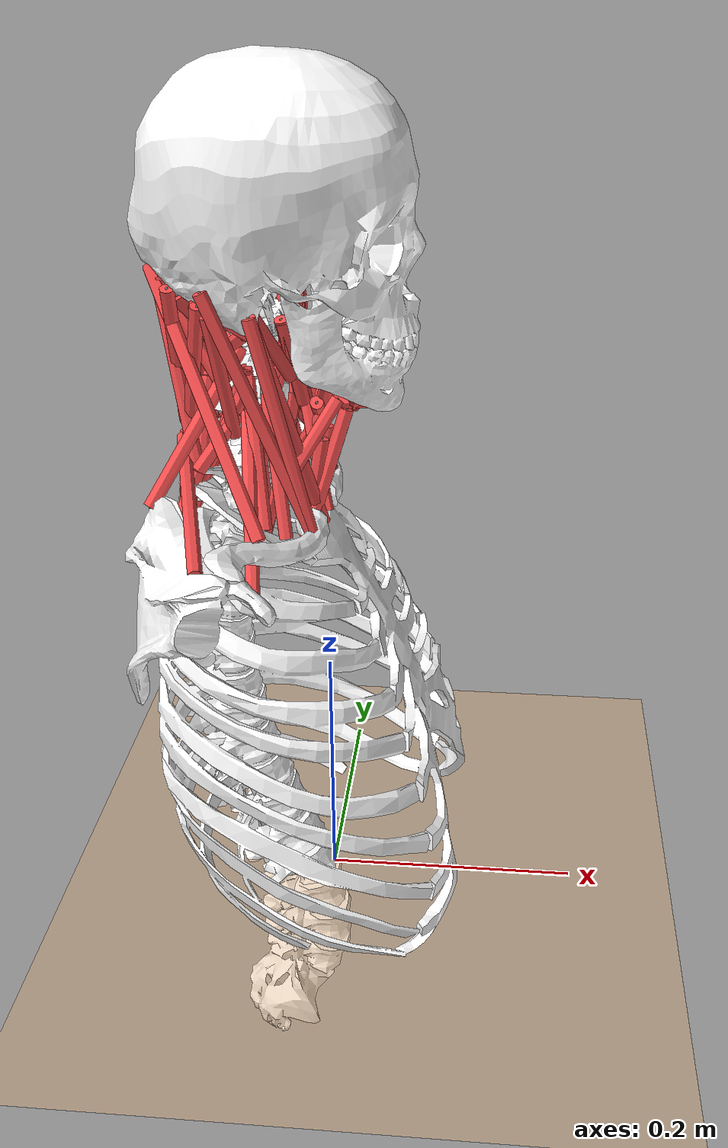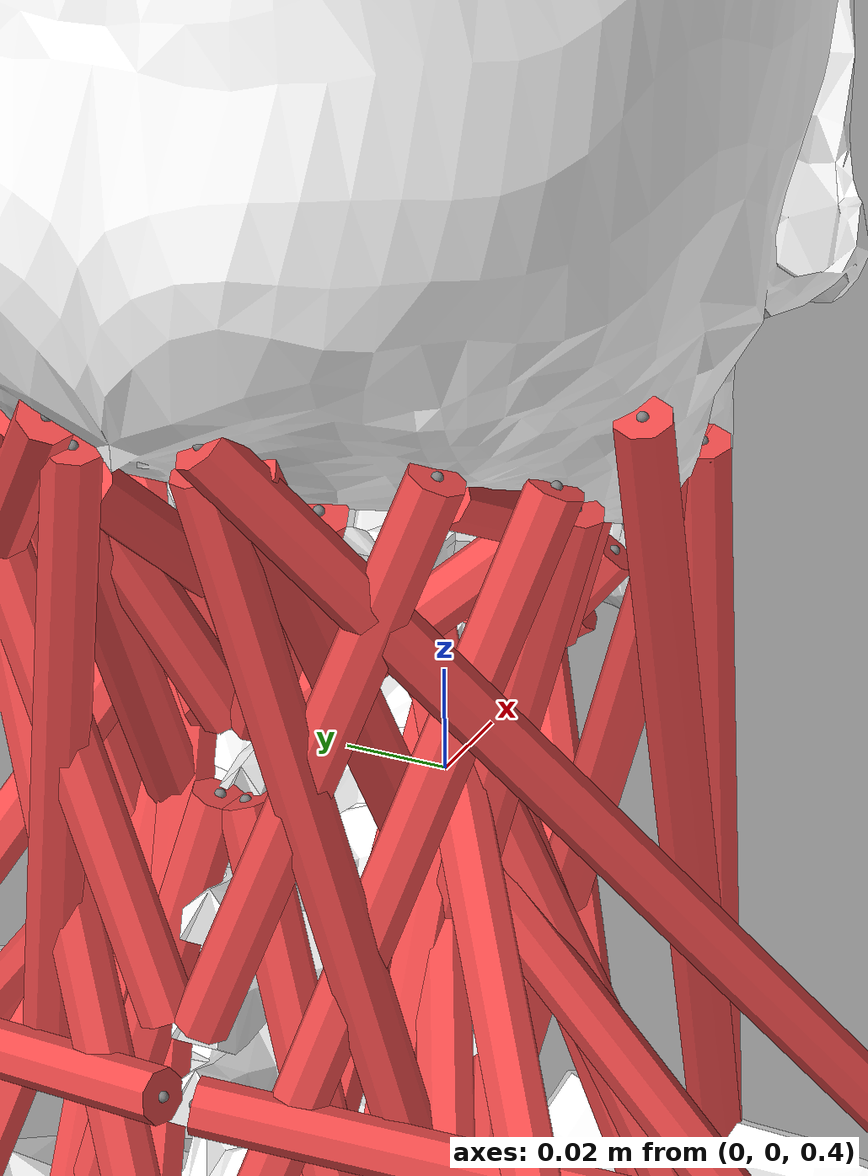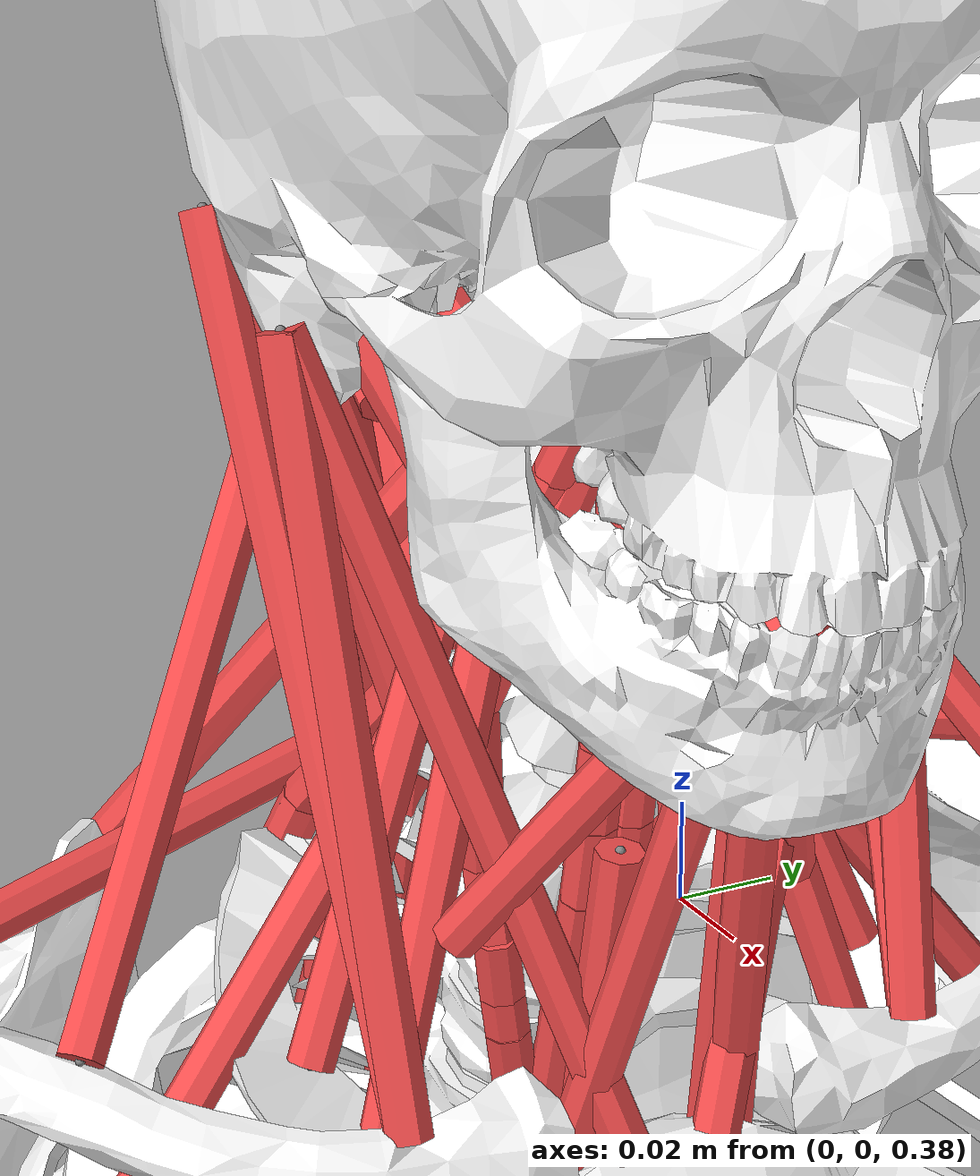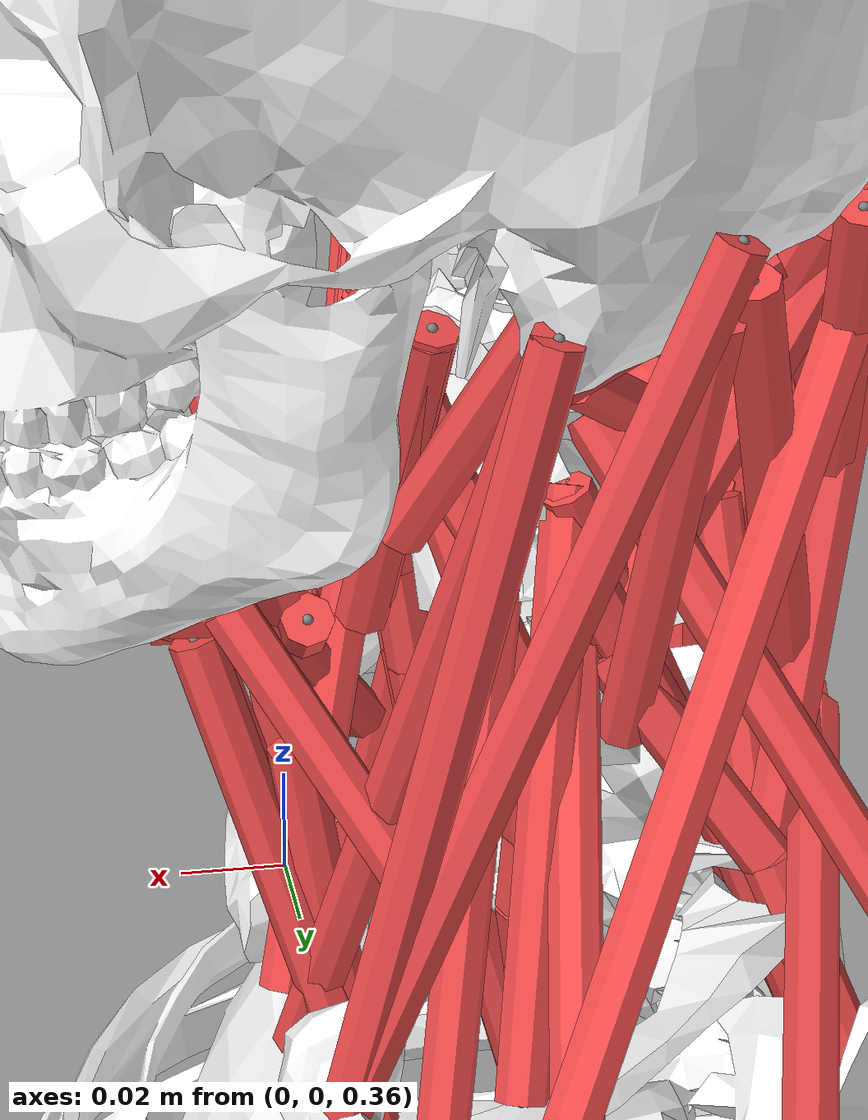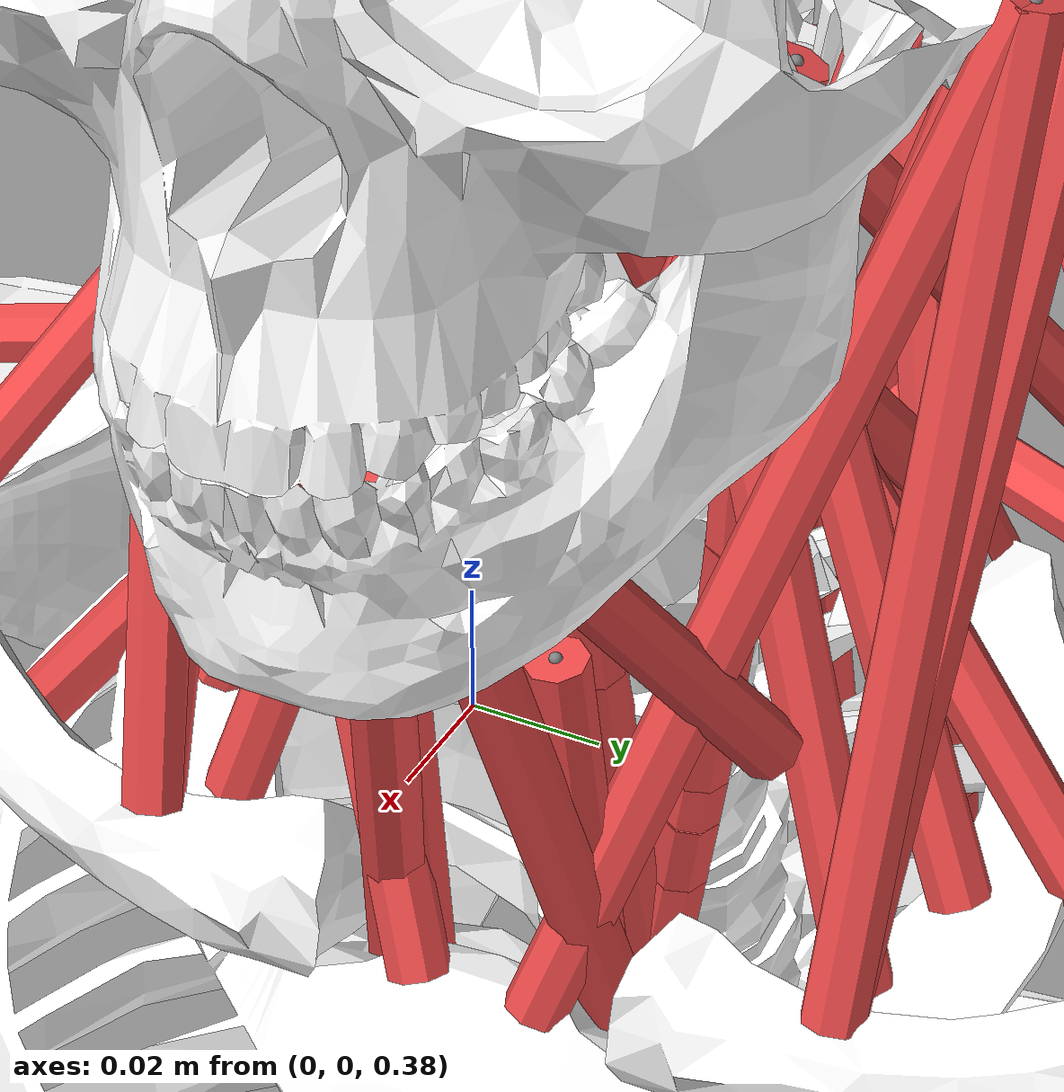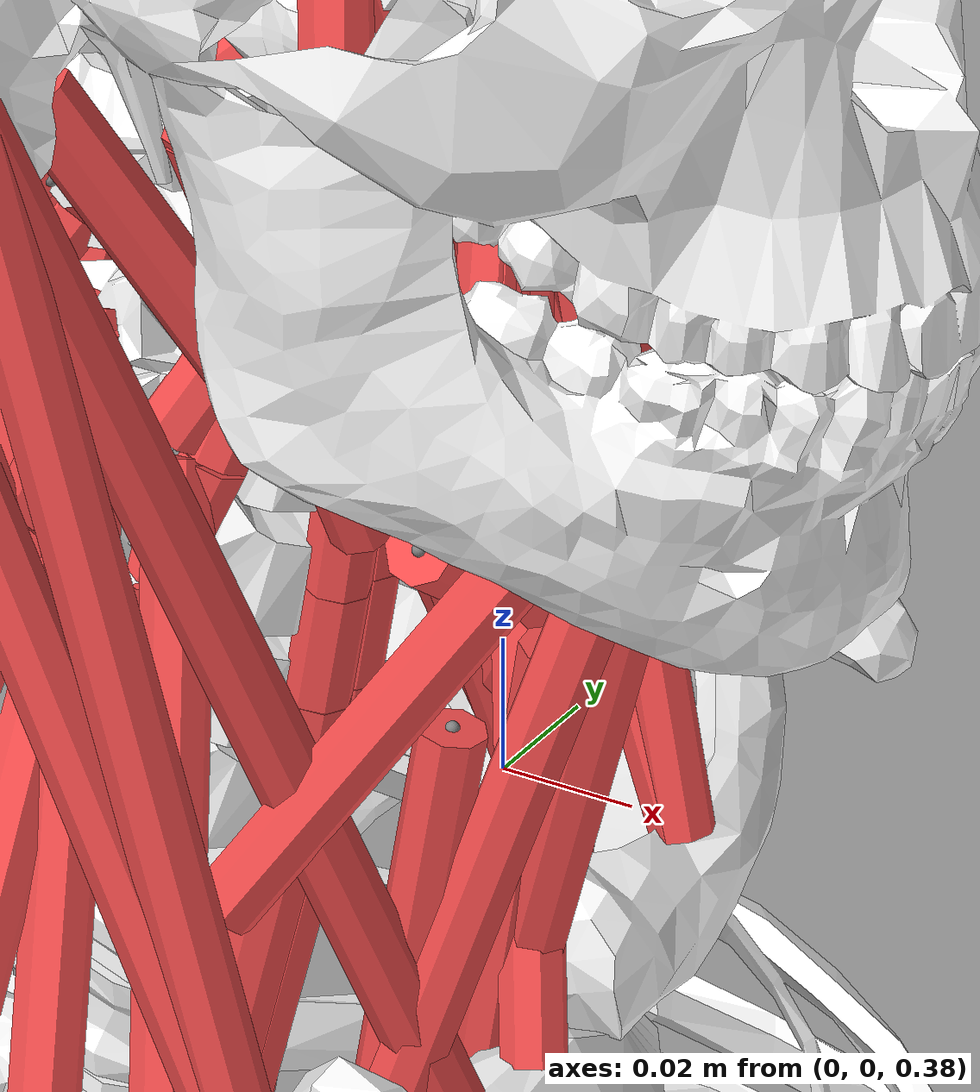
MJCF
<mujoco model="template">
    <!-- This model has been converted from an OpenSim model. Model conversion by MyoConverter https://github.com/MyoHub/myoConverter. This model is licensed under Apache 2.0. -->
    <compiler angle="radian"/>
    <option timestep="0.001" collision="predefined"/>
    <size njmax="1000" nconmax="400" nkey="1" nuser_jnt="1"/>
    <visual>
        <scale framelength="0.5" framewidth="0.01"/>
    </visual>
    <default class="main">
        <joint limited="true" armature="1e-05" damping="0.05"/>
        <geom margin="0.001" rgba="0.8 0.6 0.4 1"/>
        <site size="0.001 0.005 0.005"/>
        <tendon width="0.005" rgba="0.95 0.3 0.3 1"/>
        <default class="muscle">
            <general ctrllimited="true" ctrlrange="0 1" dyntype="muscle" gaintype="muscle" biastype="muscle" dynprm="0.01 0.04 0 0 0 0 0 0 0 0" gainprm="0.75 1.05 -1 200 0.5 1.6 1.5 1.3 1.2 0" biasprm="0.75 1.05 -1 200 0.5 1.6 1.5 1.3 1.2 0"/>
        </default>
        <default class="motor">
            <general gainprm="5 0 0 0 0 0 0 0 0 0"/>
        </default>
    </default>
    <asset>
        <texture type="skybox" builtin="gradient" rgb1="1 1 1" rgb2="0.6 0.8 1" width="256" height="1536"/>
        <mesh name="spine_geom_1_tlspine" file="Geometry/tlspine.stl"/>
        <mesh name="rscapula_geom_1_rscapula" file="Geometry/rscapula.stl"/>
        <mesh name="rclavicle_geom_1_rclavicle" file="Geometry/rclavicle.stl"/>
        <mesh name="lscapula_geom_1_lscapula" file="Geometry/lscapula.stl"/>
        <mesh name="lclavicle_geom_1_lclavicle" file="Geometry/lclavicle.stl"/>
        <mesh name="ribcage_geom_1_ribcage" file="Geometry/ribcage.stl"/>
        <mesh name="cerv7_geom_1_rotatedcerv7" file="Geometry/rotatedcerv7.stl"/>
        <mesh name="cerv6_geom_1_cerv6" file="Geometry/cerv6.stl"/>
        <mesh name="cerv5_geom_1_cerv5" file="Geometry/cerv5.stl"/>
        <mesh name="cerv4_geom_1_cerv4" file="Geometry/cerv4.stl"/>
        <mesh name="cerv3_geom_1_cerv3" file="Geometry/cerv3.stl"/>
        <mesh name="cerv2_geom_1_cerv2" file="Geometry/cerv2.stl"/>
        <mesh name="cerv1_geom_1_cerv1" file="Geometry/cerv1.stl"/>
        <mesh name="skull_geom_1_skull" file="Geometry/skull.stl"/>
        <mesh name="jaw_geom_1_jaw" file="Geometry/jaw.stl"/>
    </asset>
    <worldbody>
        <light pos="0 0 0" dir="0 0 -1" directional="true"/>
        <body name="ground" pos="0 0 0" quat="0.707035 0.707179 0 0">
            <geom name="ground-plane" size="10 10 0.125" quat="0.707035 -0.707179 0 0" type="plane" rgba="1 0.7 0.4 1"/>
        </body>
        <body name="spine" pos="0 0 0" quat="0.707035 0.707179 0 0">
            <inertial pos="0 0 0" mass="70" diaginertia="1 1 1"/>
            <joint name="spine_tx" pos="0 0 0" axis="1 0 0" type="slide" range="-1 1" damping="0"/>
            <joint name="spine_ty" pos="0 0 0" axis="0 1 0" type="slide" range="-1 1" damping="0"/>
            <joint name="spine_tz" pos="0 0 0" axis="0 0 1" type="slide" range="-1 1" damping="0"/>
            <joint name="gndpitch" pos="0 0 0" axis="0 0 1" range="-3.142 3.142" damping="0" user="7.35301e-11"/>
            <joint name="gndroll" pos="0 0 0" axis="1 0 0" range="-3.142 3.142" damping="0" user="1.39669e-11"/>
            <joint name="gndyaw" pos="0 0 0" axis="0 1 0" range="-3.142 3.142" damping="0" user="7.7499e-12"/>
            <geom name="spine_geom_1" type="mesh" rgba="1 1 1 1" mesh="spine_geom_1_tlspine"/>
            <site name="long_col_c1thx_long_col_c1thx-P1" pos="-0.04888 0.30334 0.0037"/>
            <site name="long_col_c1thx_L_long_col_c1thx_L-P1" pos="-0.04888 0.30334 -0.0037"/>
            <site name="long_col_c5thx_long_col_c5thx-P1" pos="-0.04981 0.30296 0.0068"/>
            <site name="long_col_c5thx_long_col_c5thx-P2" pos="-0.04825 0.32027 0.01022"/>
            <site name="long_col_c5thx_long_col_c5thx-P3" pos="-0.04566 0.33463 0.01337"/>
            <site name="long_col_c5thx_long_col_c5thx-P4" pos="-0.04466 0.3436 0.01508"/>
            <site name="long_col_c5thx_long_col_c5thx-P5" pos="-0.04239 0.35783 0.01778"/>
            <site name="long_col_c5thx_L_long_col_c5thx_L-P1" pos="-0.04981 0.30296 -0.0068"/>
            <site name="long_col_c5thx_L_long_col_c5thx_L-P2" pos="-0.04825 0.32027 -0.01022"/>
            <site name="long_col_c5thx_L_long_col_c5thx_L-P3" pos="-0.04566 0.33463 -0.01337"/>
            <site name="long_col_c5thx_L_long_col_c5thx_L-P4" pos="-0.04466 0.3436 -0.01508"/>
            <site name="long_col_c5thx_L_long_col_c5thx_L-P5" pos="-0.04239 0.35783 -0.01778"/>
            <site name="splen_cap_sklthx_splen_cap_sklthx-P1" pos="-0.10384 0.33902 0.003"/>
            <site name="splen_cap_sklthx_L_splen_cap_sklthx_L-P1" pos="-0.10384 0.33902 -0.003"/>
            <site name="splen_cerv_c3thx_splen_cerv_c3thx-P1" pos="-0.12848 0.26222 0.0041"/>
            <site name="splen_cerv_c3thx_L_splen_cerv_c3thx_L-P1" pos="-0.12848 0.26222 -0.0041"/>
            <site name="semi_cap_sklthx_semi_cap_sklthx-P1" pos="-0.08539 0.37732 0.0347"/>
            <site name="semi_cap_sklthx_L_semi_cap_sklthx_L-P1" pos="-0.08539 0.37732 -0.0347"/>
            <site name="semi_cerv_c3thx_semi_cerv_c3thx-P1" pos="-0.08896 0.34997 0.02607"/>
            <site name="semi_cerv_c3thx_L_semi_cerv_c3thx_L-P1" pos="-0.08896 0.34997 -0.02607"/>
            <site name="longissi_cerv_c4thx_longissi_cerv_c4thx-P1" pos="-0.10994 0.27586 0.03215"/>
            <site name="longissi_cerv_c4thx_longissi_cerv_c4thx-P2" pos="-0.10918 0.30238 0.03041"/>
            <site name="longissi_cerv_c4thx_longissi_cerv_c4thx-P3" pos="-0.09978 0.32692 0.02919"/>
            <site name="longissi_cerv_c4thx_longissi_cerv_c4thx-P4" pos="-0.0813 0.373 0.0279"/>
            <site name="longissi_cerv_c4thx_L_longissi_cerv_c4thx_L-P1" pos="-0.10994 0.27586 -0.03215"/>
            <site name="longissi_cerv_c4thx_L_longissi_cerv_c4thx_L-P2" pos="-0.10918 0.30238 -0.03041"/>
            <site name="longissi_cerv_c4thx_L_longissi_cerv_c4thx_L-P3" pos="-0.09978 0.32692 -0.02919"/>
            <site name="longissi_cerv_c4thx_L_longissi_cerv_c4thx_L-P4" pos="-0.0813 0.373 -0.0279"/>
            <site name="iliocost_cerv_c5rib_iliocost_cerv_c5rib-P1" pos="-0.10349 0.32797 0.0533"/>
            <site name="iliocost_cerv_c5rib_iliocost_cerv_c5rib-P2" pos="-0.08374 0.37638 0.04035"/>
            <site name="iliocost_cerv_c5rib_L_iliocost_cerv_c5rib_L-P1" pos="-0.10349 0.32797 -0.0533"/>
            <site name="iliocost_cerv_c5rib_L_iliocost_cerv_c5rib_L-P2" pos="-0.08374 0.37638 -0.04035"/>
            <body name="rscapula" pos="-0.0366 0.3623 0.1837" quat="0.980384 0.0986852 -0.139174 -0.0986852">
                <inertial pos="0 0 0" mass="1" diaginertia="1 1 0.5"/>
                <geom name="rscapula_geom_1" type="mesh" rgba="1 1 1 1" mesh="rscapula_geom_1_rscapula"/>
                <site name="trap_acr_trap_acr-P1" pos="-0.02379 -0.00916 -0.00736"/>
                <site name="levator_scap_levator_scap-P1" pos="-0.09749 -0.03624 -0.08146"/>
                <site name="RCAJ_marker" pos="0 0.01 0.02" size="0.01" group="4" rgba="1 0.1 0.5 0.5"/>
            </body>
            <body name="rclavicle" pos="-0.0118 0.3353 0.022" quat="0.997565 0 0.0697433 0">
                <inertial pos="0 0 0" mass="1" diaginertia="1 1 0.5"/>
                <geom name="rclavicle_geom_1" type="mesh" rgba="1 1 1 1" mesh="rclavicle_geom_1_rclavicle"/>
                <site name="cleid_mast_cleid_mast-P1" pos="0.00388 0.00542 0.0352"/>
                <site name="cleid_occ_cleid_occ-P1" pos="0.00388 0.00542 0.0352"/>
                <site name="trap_cl_trap_cl-P1" pos="-0.0294 0.0232 0.0869"/>
            </body>
            <body name="lscapula" pos="-0.0366 0.3623 -0.1837" quat="0.980384 -0.0986852 0.139174 -0.0986852">
                <inertial pos="0 0 0" mass="1" diaginertia="1 1 0.5"/>
                <geom name="lscapula_geom_1" type="mesh" rgba="1 1 1 1" mesh="lscapula_geom_1_lscapula"/>
                <site name="trap_acr_L_trap_acr_L-P1" pos="-0.02379 -0.00916 0.00736"/>
                <site name="levator_scap_L_levator_scap_L-P1" pos="-0.09749 -0.03624 0.08146"/>
                <site name="LCAJ_marker" pos="0 0.01 -0.02" size="0.01" group="4" rgba="1 0.1 0.5 0.5"/>
            </body>
            <body name="lclavicle" pos="-0.0118 0.3353 -0.022" quat="0.997565 0 -0.0697433 0">
                <inertial pos="0 0 0" mass="1" diaginertia="1 1 0.5"/>
                <geom name="lclavicle_geom_1" type="mesh" rgba="1 1 1 1" mesh="lclavicle_geom_1_lclavicle"/>
                <site name="cleid_mast_L_cleid_mast_L-P1" pos="0.00388 0.00542 -0.0352"/>
                <site name="cleid_occ_L_cleid_occ_L-P1" pos="0.00388 0.00542 -0.0352"/>
                <site name="trap_cl_L_trap_cl_L-P1" pos="-0.0294 0.0232 -0.0869"/>
            </body>
            <body name="ribcage" pos="0 0 0">
                <inertial pos="0 0 0" mass="1" diaginertia="1 1 0.75"/>
                <geom name="ribcage_geom_1" type="mesh" rgba="1 1 1 1" mesh="ribcage_geom_1_ribcage"/>
                <site name="Sterno_hyoid_default" pos="-0.014033 0.31252 0.01984"/>
                <site name="SternoThyroid_default" pos="-0.014643 0.30575 0.0153"/>
                <site name="Omo_hyoid_default" pos="-0.021033 0.37083 0.03774"/>
                <site name="Sterno_hyoid_L_default" pos="-0.014033 0.31252 -0.01984"/>
                <site name="SternoThyroid_L_default" pos="-0.014643 0.30575 -0.0153"/>
                <site name="Omo_hyoid_L_default" pos="-0.021033 0.37083 -0.03774"/>
                <site name="stern_mast_stern_mast-P1" pos="-0.0007 0.3269 0.0096"/>
                <site name="stern_mast_L_stern_mast_L-P1" pos="-0.0007 0.3269 -0.0096"/>
                <site name="scalenus_ant_scalenus_ant-P1" pos="-0.02139 0.33246 0.0529"/>
                <site name="scalenus_ant_L_scalenus_ant_L-P1" pos="-0.02139 0.33246 -0.0529"/>
                <site name="scalenus_med_scalenus_med-P1" pos="-0.03398 0.34333 0.0627"/>
                <site name="scalenus_med_L_scalenus_med_L-P1" pos="-0.03398 0.34333 -0.0627"/>
                <site name="scalenus_post_scalenus_post-P1" pos="-0.03638 0.3127 0.1062"/>
                <site name="scalenus_post_L_scalenus_post_L-P1" pos="-0.03638 0.3127 -0.1062"/>
                <site name="SJN_marker" pos="0.02 0.3516 0" size="0.01" group="4" rgba="1 0.1 0.5 0.5"/>
            </body>
            <body name="cerv7" pos="-0.05434 0.367 0">
                <inertial pos="-0.0002 0.0071 0" quat="0.707107 0 0 0.707107" mass="0.584085" diaginertia="0.04 0.04 0.04"/>
                <joint name="pitch2" pos="0 0 0" axis="0 0 1" range="-0.05702 0.08294" user="1.18003e-07"/>
                <joint name="roll2" pos="0 0 0" axis="1 0 0" range="-0.04492 0.04492"/>
                <joint name="yaw2" pos="0 0 0" axis="0 1 0" range="-0.02969 0.02969"/>
                <geom name="cerv7_geom_1" type="mesh" rgba="1 1 1 1" mesh="cerv7_geom_1_rotatedcerv7"/>
                <site name="long_col_c1thx_long_col_c1thx-P2" pos="0.0232 0.0011 0.004"/>
                <site name="long_col_c1thx_L_long_col_c1thx_L-P2" pos="0.0232 0.0011 -0.004"/>
                <site name="long_col_c5thx_long_col_c5thx-P6" pos="0.01111 0.00731 0.01979"/>
                <site name="long_col_c5thx_L_long_col_c5thx_L-P6" pos="0.01111 0.00731 -0.01979"/>
                <site name="trap_acr_trap_acr-P2" pos="-0.0477 0.019 0.00305"/>
                <site name="trap_acr_L_trap_acr_L-P2" pos="-0.0477 0.019 -0.00305"/>
                <body name="cerv6" pos="0.003837 0.01645 0">
                    <inertial pos="0.0002 0.0064 0" quat="0.707107 0 0 0.707107" mass="0.507749" diaginertia="0.04 0.04 0.04"/>
                    <joint name="aux7jnt_r3" pos="0 0 0" axis="0 0 1" limited="false" range="-1.57 1.57" user="2.22895e-07"/>
                    <joint name="aux7jnt_r1" pos="0 0 0" axis="1 0 0" limited="false" range="-1.57 1.57"/>
                    <joint name="aux7jnt_r2" pos="0 0 0" axis="0 1 0" limited="false" range="-1.57 1.57"/>
                    <geom name="cerv6_geom_1" type="mesh" rgba="1 1 1 1" mesh="cerv6_geom_1_cerv6"/>
                    <site name="long_col_c1thx_long_col_c1thx-P3" pos="0.02314 0.00231 0.00402"/>
                    <site name="long_col_c1thx_L_long_col_c1thx_L-P3" pos="0.02314 0.00231 -0.00402"/>
                    <site name="long_col_c5thx_long_col_c5thx-P7" pos="0.00961 0.00713 0.02216"/>
                    <site name="long_col_c5thx_L_long_col_c5thx_L-P7" pos="0.00961 0.00713 -0.02216"/>
                    <site name="splen_cap_sklc6_splen_cap_sklc6-P1" pos="-0.0486 0.01647 0.00305"/>
                    <site name="splen_cap_sklc6_L_splen_cap_sklc6_L-P1" pos="-0.0486 0.01647 -0.00305"/>
                    <site name="longissi_cap_sklc6_longissi_cap_sklc6-P1" pos="-0.00817 0.01515 0.02759"/>
                    <site name="longissi_cap_sklc6_L_longissi_cap_sklc6_L-P1" pos="-0.00817 0.01515 -0.02759"/>
                    <body name="cerv5" pos="0.00418 0.0179 0">
                        <inertial pos="0.0001 0.0063 0" quat="0.707107 0 0 0.707107" mass="0.4291" diaginertia="0.04 0.04 0.04"/>
                        <joint name="aux6jnt_r3" pos="0 0 0" axis="0 0 1" limited="false" range="-1.57 1.57" user="2.62229e-07"/>
                        <joint name="aux6jnt_r1" pos="0 0 0" axis="1 0 0" limited="false" range="-1.57 1.57"/>
                        <joint name="aux6jnt_r2" pos="0 0 0" axis="0 1 0" limited="false" range="-1.57 1.57"/>
                        <geom name="cerv5_geom_1" type="mesh" rgba="1 1 1 1" mesh="cerv5_geom_1_cerv5"/>
                        <site name="scalenus_post_scalenus_post-P2" pos="-0.0032 0.01371 0.0257"/>
                        <site name="scalenus_post_L_scalenus_post_L-P2" pos="-0.0032 0.01371 -0.0257"/>
                        <site name="long_col_c1thx_long_col_c1thx-P4" pos="0.02228 0.00228 0.0039"/>
                        <site name="long_col_c1thx_L_long_col_c1thx_L-P4" pos="0.02228 0.00228 -0.0039"/>
                        <site name="long_col_c1c5_long_col_c1c5-P1" pos="0.00669 0.00889 0.0238"/>
                        <site name="long_col_c1c5_L_long_col_c1c5_L-P1" pos="0.00669 0.00889 -0.0238"/>
                        <site name="long_col_c5thx_long_col_c5thx-P8" pos="0.00669 0.00889 0.0238"/>
                        <site name="long_col_c5thx_L_long_col_c5thx_L-P8" pos="0.00669 0.00889 -0.0238"/>
                        <site name="semi_cap_sklc5_semi_cap_sklc5-P1" pos="-0.00931 0.01154 0.0235"/>
                        <site name="semi_cap_sklc5_L_semi_cap_sklc5_L-P1" pos="-0.00931 0.01154 -0.0235"/>
                        <site name="iliocost_cerv_c5rib_iliocost_cerv_c5rib-P3" pos="-0.0094 0.01258 0.026"/>
                        <site name="iliocost_cerv_c5rib_L_iliocost_cerv_c5rib_L-P3" pos="-0.0094 0.01258 -0.026"/>
                        <body name="cerv4" pos="0.00341 0.01917 0">
                            <inertial pos="-0.0003 0.0067 0" quat="0.707107 0 0 0.707107" mass="0.423317" diaginertia="0.04 0.04 0.04"/>
                            <joint name="aux5jnt_r3" pos="0 0 0" axis="0 0 1" limited="false" range="-1.57 1.57" user="2.62229e-07"/>
                            <joint name="aux5jnt_r1" pos="0 0 0" axis="1 0 0" limited="false" range="-1.57 1.57"/>
                            <joint name="aux5jnt_r2" pos="0 0 0" axis="0 1 0" limited="false" range="-1.57 1.57"/>
                            <geom name="cerv4_geom_1" type="mesh" rgba="1 1 1 1" mesh="cerv4_geom_1_cerv4"/>
                            <site name="scalenus_ant_scalenus_ant-P2" pos="0.00713 0.0079 0.02323"/>
                            <site name="scalenus_ant_L_scalenus_ant_L-P2" pos="0.00713 0.0079 -0.02323"/>
                            <site name="long_cap_sklc4_long_cap_sklc4-P1" pos="0.00652 0.01164 0.0242"/>
                            <site name="long_cap_sklc4_L_long_cap_sklc4_L-P1" pos="0.00652 0.01164 -0.0242"/>
                            <site name="long_col_c1thx_long_col_c1thx-P5" pos="0.02205 0.00331 0.00379"/>
                            <site name="long_col_c1thx_L_long_col_c1thx_L-P5" pos="0.02205 0.00331 -0.00379"/>
                            <site name="long_col_c1c5_long_col_c1c5-P2" pos="0.01121 0.00749 0.0207"/>
                            <site name="long_col_c1c5_L_long_col_c1c5_L-P2" pos="0.01121 0.00749 -0.0207"/>
                            <site name="longissi_cerv_c4thx_longissi_cerv_c4thx-P5" pos="-0.00709 0.01157 0.0261"/>
                            <site name="longissi_cerv_c4thx_L_longissi_cerv_c4thx_L-P5" pos="-0.00709 0.01157 -0.0261"/>
                            <body name="cerv3" pos="0.00261 0.0154 0">
                                <inertial pos="-0.0008 0.0071 0" quat="0.707107 0 0 0.707107" mass="0.419847" diaginertia="0.04 0.04 0.04"/>
                                <joint name="aux4jnt_r3" pos="0 0 0" axis="0 0 1" limited="false" range="-1.57 1.57" user="1.96672e-07"/>
                                <joint name="aux4jnt_r1" pos="0 0 0" axis="1 0 0" limited="false" range="-1.57 1.57"/>
                                <joint name="aux4jnt_r2" pos="0 0 0" axis="0 1 0" limited="false" range="-1.57 1.57"/>
                                <geom name="cerv3_geom_1" type="mesh" rgba="1 1 1 1" mesh="cerv3_geom_1_cerv3"/>
                                <site name="digastric_post_digastricpost-P2" pos="0.02321 0.00597 0.0287"/>
                                <site name="Sterno_hyoid_stern_mast-P1" pos="0.05742 -0.02314 0.00629"/>
                                <site name="SternoThyroid_stern_mast-P1" pos="0.0404201 -0.04316 0.0133"/>
                                <site name="Omo_hyoid_stern_mast-P1" pos="0.05212 -0.0139 0.0132"/>
                                <site name="digastric_post_L_digastricpost-P2" pos="0.02321 0.00597 -0.0287"/>
                                <site name="Sterno_hyoid_L_stern_mast-P1" pos="0.05742 -0.02314 -0.00629"/>
                                <site name="SternoThyroid_L_stern_mast-P1" pos="0.0404201 -0.04316 -0.0133"/>
                                <site name="Omo_hyoid_L_stern_mast-P1" pos="0.05212 -0.0139 -0.0132"/>
                                <site name="scalenus_med_scalenus_med-P2" pos="-0.00902 0.00981 0.02119"/>
                                <site name="scalenus_med_L_scalenus_med_L-P2" pos="-0.00902 0.00981 -0.02119"/>
                                <site name="long_cap_sklc4_long_cap_sklc4-P2" pos="0.01197 0.01009 0.01897"/>
                                <site name="long_cap_sklc4_L_long_cap_sklc4_L-P2" pos="0.01197 0.01009 -0.01897"/>
                                <site name="long_col_c1thx_long_col_c1thx-P6" pos="0.02212 0.00603 0.00368"/>
                                <site name="long_col_c1thx_L_long_col_c1thx_L-P6" pos="0.02212 0.00603 -0.00368"/>
                                <site name="splen_cerv_c3thx_splen_cerv_c3thx-P2" pos="-0.00787 0.01005 0.02365"/>
                                <site name="splen_cerv_c3thx_L_splen_cerv_c3thx_L-P2" pos="-0.00787 0.01005 -0.02365"/>
                                <site name="semi_cerv_c3thx_semi_cerv_c3thx-P2" pos="-0.04064 -0.00322 0.0024"/>
                                <site name="semi_cerv_c3thx_L_semi_cerv_c3thx_L-P2" pos="-0.04064 -0.00322 -0.0024"/>
                                <body name="cerv2" pos="-0.00018 0.01629 0">
                                    <inertial pos="-0.001 0.0059 0" quat="0.707107 0 0 0.707107" mass="0.587554" diaginertia="0.04 0.04 0.04"/>
                                    <joint name="aux3jnt_r3" pos="0 0 0" axis="0 0 1" limited="false" range="-1.57 1.57" user="1.31115e-07"/>
                                    <joint name="aux3jnt_r1" pos="0 0 0" axis="1 0 0" limited="false" range="-1.57 1.57"/>
                                    <joint name="aux3jnt_r2" pos="0 0 0" axis="0 1 0" limited="false" range="-1.57 1.57"/>
                                    <geom name="cerv2_geom_1" type="mesh" rgba="1 1 1 1" mesh="cerv2_geom_1_cerv2"/>
                                    <site name="long_cap_sklc4_long_cap_sklc4-P3" pos="0.0172 0.00829 0.01477"/>
                                    <site name="long_cap_sklc4_L_long_cap_sklc4_L-P3" pos="0.0172 0.00829 -0.01477"/>
                                    <site name="long_col_c1thx_long_col_c1thx-P7" pos="0.02122 0.00973 0.00356"/>
                                    <site name="long_col_c1thx_L_long_col_c1thx_L-P7" pos="0.02122 0.00973 -0.00356"/>
                                    <site name="long_col_c1c5_long_col_c1c5-P3" pos="0.01739 0.00159 0.01365"/>
                                    <site name="long_col_c1c5_L_long_col_c1c5_L-P3" pos="0.01739 0.00159 -0.01365"/>
                                    <site name="levator_scap_levator_scap-P2" pos="-0.01186 0.00725 0.02121"/>
                                    <site name="levator_scap_L_levator_scap_L-P2" pos="-0.01186 0.00725 -0.02121"/>
                                    <site name="rectcap_post_maj_rectcap_post_maj-P1" pos="-0.03637 -0.00647 0.0024"/>
                                    <site name="rectcap_post_maj_L_rectcap_post_maj_L-P1" pos="-0.03637 -0.00647 -0.0024"/>
                                    <site name="obl_cap_inf_obl_cap_inf-P1" pos="-0.03637 -0.00647 0.00547"/>
                                    <site name="obl_cap_inf_L_obl_cap_inf_L-P1" pos="-0.03637 -0.00647 -0.00547"/>
                                    <body name="cerv1" pos="-0.03556 0.01776 0">
                                        <inertial pos="0.0312 0.0019 0" quat="0.707107 0 0 0.707107" mass="0.467268" diaginertia="0.04 0.04 0.04"/>
                                        <joint name="pitch1" pos="0 0 0" axis="0 0 1" range="-0.124 0.186" user="6.98927e-07"/>
                                        <joint name="roll1" pos="0 0 0" axis="1 0 0" range="-0.05236 0.05236"/>
                                        <joint name="yaw1" pos="0 0 0" axis="0 1 0" range="-0.5896 0.5896"/>
                                        <geom name="cerv1_geom_1" type="mesh" rgba="1 1 1 1" mesh="cerv1_geom_1_cerv1"/>
                                        <site name="digastric_ant_digastricpost-P2" pos="0.07289 -0.05758 0.0057"/>
                                        <site name="Geniohyoid_digastricpost-P1" pos="0.0717298 -0.0537906 0.00509443"/>
                                        <site name="Mylohyoid_Post_digastricpost-P1" pos="0.07525 -0.05588 0.0031"/>
                                        <site name="Mylohyoid_Ant_digastricpost-P1" pos="0.09725 -0.05668 -0.0031"/>
                                        <site name="Stylohyoid_Lat_digastricpost-P2" pos="0.0643381 -0.0496832 0.01544"/>
                                        <site name="Stylohyoid_Med_digastricpost-P2" pos="0.0632661 -0.0450538 0.0162521"/>
                                        <site name="digastric_ant_L_digastricpost-P2" pos="0.07289 -0.05758 -0.0057"/>
                                        <site name="Geniohyoid_L_digastricpost-P1" pos="0.0714947 -0.0538159 -0.00630312"/>
                                        <site name="Mylohyoid_Post_L_digastricpost-P1" pos="0.07525 -0.05588 -0.0031"/>
                                        <site name="Mylohyoid_Ant_L_digastricpost-P1" pos="0.09725 -0.05668 0.0031"/>
                                        <site name="Stylohyoid_Lat_L_digastricpost-P2" pos="0.0636822 -0.0497536 -0.0163531"/>
                                        <site name="Stylohyoid_Med_L_digastricpost-P2" pos="0.0625772 -0.0451277 -0.0171408"/>
                                        <site name="long_cap_sklc4_long_cap_sklc4-P4" pos="0.05818 0.00309 0.01159"/>
                                        <site name="long_cap_sklc4_L_long_cap_sklc4_L-P4" pos="0.05818 0.00309 -0.01159"/>
                                        <site name="long_col_c1thx_long_col_c1thx-P8" pos="0.05825 0.00482 0.0031"/>
                                        <site name="long_col_c1thx_L_long_col_c1thx_L-P8" pos="0.05825 0.00482 -0.0031"/>
                                        <site name="long_col_c1c5_long_col_c1c5-P4" pos="0.05725 0.00482 0.0062"/>
                                        <site name="long_col_c1c5_L_long_col_c1c5_L-P4" pos="0.05725 0.00482 -0.0062"/>
                                        <site name="rectcap_post_min_rectcap_post_min-P1" pos="7e-05 0.0009 0.0061"/>
                                        <site name="rectcap_post_min_L_rectcap_post_min_L-P1" pos="7e-05 0.0009 -0.0061"/>
                                        <site name="obl_cap_sup_obl_cap_sup-P1" pos="0.03505 0.00385 0.042"/>
                                        <site name="obl_cap_sup_L_obl_cap_sup_L-P1" pos="0.03505 0.00385 -0.042"/>
                                        <site name="obl_cap_inf_obl_cap_inf-P2" pos="0.02996 0.00349 0.03791"/>
                                        <site name="obl_cap_inf_L_obl_cap_inf_L-P2" pos="0.02996 0.00349 -0.03791"/>
                                        <body name="skull" pos="0.04335 0.01492 0">
                                            <inertial pos="0.0173 0.063 0" quat="0.5 0.5 -0.5 0.5" mass="4.3" diaginertia="0.022605 0.02073 0.015"/>
                                            <joint name="aux1jnt_r3" pos="0 0 0" axis="0 0 1" limited="false" range="-1.57 1.57" user="8.75233e-07"/>
                                            <joint name="aux1jnt_r1" pos="0 0 0" axis="1 0 0" limited="false" range="-1.57 1.57"/>
                                            <joint name="aux1jnt_r2" pos="0 0 0" axis="0 1 0" limited="false" range="-1.57 1.57"/>
                                            <geom name="skull_geom_1" type="mesh" rgba="1 1 1 1" mesh="skull_geom_1_skull"/>
                                            <site name="digastric_post_digastricpost-P1" pos="-0.0061 0.0034 0.0477"/>
                                            <site name="digastric_ant_digastricpost-P1" pos="0.0303 -0.0643 0.0173"/>
                                            <site name="Geniohyoid_digastricpost-P2" pos="0.0691 -0.0673 0.0016"/>
                                            <site name="Mylohyoid_Post_digastricpost-P2" pos="0.0413 -0.0389 0.0291"/>
                                            <site name="Mylohyoid_Ant_digastricpost-P2" pos="0.0579 -0.0596 0.0158"/>
                                            <site name="Stylohyoid_Lat_digastricpost-P1" pos="0.0113 -0.0008 0.0376"/>
                                            <site name="Stylohyoid_Med_digastricpost-P1" pos="0.0118 -0.002 0.0376"/>
                                            <site name="digastric_post_L_digastricpost-P1" pos="-0.0061 0.0034 -0.0477"/>
                                            <site name="digastric_ant_L_digastricpost-P1" pos="0.0303 -0.0643 -0.0173"/>
                                            <site name="Geniohyoid_L_digastricpost-P2" pos="0.0691 -0.0673 -0.0016"/>
                                            <site name="Mylohyoid_Post_L_digastricpost-P2" pos="0.0413 -0.0389 -0.0291"/>
                                            <site name="Mylohyoid_Ant_L_digastricpost-P2" pos="0.0579 -0.0596 -0.0158"/>
                                            <site name="Stylohyoid_Lat_L_digastricpost-P1" pos="0.0113 -0.0008 -0.0376"/>
                                            <site name="Stylohyoid_Med_L_digastricpost-P1" pos="0.0118 -0.002 -0.0376"/>
                                            <site name="stern_mast_stern_mast-P2" pos="-0.0051 0.00693 0.0643"/>
                                            <site name="stern_mast_L_stern_mast_L-P2" pos="-0.0051 0.00693 -0.0643"/>
                                            <site name="cleid_mast_cleid_mast-P2" pos="-0.0051 0.00693 0.0643"/>
                                            <site name="cleid_mast_L_cleid_mast_L-P2" pos="-0.0051 0.00693 -0.0643"/>
                                            <site name="cleid_occ_cleid_occ-P2" pos="-0.035 0.023 0.0664"/>
                                            <site name="cleid_occ_L_cleid_occ_L-P2" pos="-0.035 0.023 -0.0664"/>
                                            <site name="long_cap_sklc4_long_cap_sklc4-P5" pos="0.0098 0.01596 0.0036"/>
                                            <site name="long_cap_sklc4_L_long_cap_sklc4_L-P5" pos="0.0098 0.01596 -0.0036"/>
                                            <site name="trap_cl_trap_cl-P2" pos="-0.08031 0.02604 0.01324"/>
                                            <site name="trap_cl_L_trap_cl_L-P2" pos="-0.08031 0.02604 -0.01324"/>
                                            <site name="splen_cap_sklc6_splen_cap_sklc6-P2" pos="-0.06164 0.01918 0.044"/>
                                            <site name="splen_cap_sklc6_L_splen_cap_sklc6_L-P2" pos="-0.06164 0.01918 -0.044"/>
                                            <site name="splen_cap_sklthx_splen_cap_sklthx-P2" pos="-0.04016 0.011 0.05423"/>
                                            <site name="splen_cap_sklthx_L_splen_cap_sklthx_L-P2" pos="-0.04016 0.011 -0.05423"/>
                                            <site name="semi_cap_sklc5_semi_cap_sklc5-P2" pos="-0.07441 0.02 0.018"/>
                                            <site name="semi_cap_sklc5_L_semi_cap_sklc5_L-P2" pos="-0.07441 0.02 -0.018"/>
                                            <site name="semi_cap_sklthx_semi_cap_sklthx-P2" pos="-0.07671 0.02 0.0111"/>
                                            <site name="semi_cap_sklthx_L_semi_cap_sklthx_L-P2" pos="-0.07671 0.02 -0.0111"/>
                                            <site name="longissi_cap_sklc6_longissi_cap_sklc6-P2" pos="-0.0344 0.0051 0.055"/>
                                            <site name="longissi_cap_sklc6_L_longissi_cap_sklc6_L-P2" pos="-0.0344 0.0051 -0.055"/>
                                            <site name="rectcap_post_maj_rectcap_post_maj-P2" pos="-0.0604 0.009 0.023"/>
                                            <site name="rectcap_post_maj_L_rectcap_post_maj_L-P2" pos="-0.0604 0.009 -0.023"/>
                                            <site name="rectcap_post_min_rectcap_post_min-P2" pos="-0.0667 0.009 0.0145"/>
                                            <site name="rectcap_post_min_L_rectcap_post_min_L-P2" pos="-0.0667 0.009 -0.0145"/>
                                            <site name="obl_cap_sup_obl_cap_sup-P2" pos="-0.04758 0.00931 0.03818"/>
                                            <site name="obl_cap_sup_L_obl_cap_sup_L-P2" pos="-0.04758 0.00931 -0.03818"/>
                                            <site name="RAH_marker" pos="0.1 0.1 0.05" size="0.01" group="4" rgba="1 0.1 0.5 0.5"/>
                                            <site name="LAH_marker" pos="0.1 0.1 -0.06" size="0.01" group="4" rgba="1 0.1 0.5 0.5"/>
                                            <site name="RPH_marker" pos="-0.09 0.1 0.045" size="0.01" group="4" rgba="1 0.1 0.5 0.5"/>
                                            <site name="LPH_marker" pos="-0.09 0.1 -0.045" size="0.01" group="4" rgba="1 0.1 0.5 0.5"/>
                                            <body name="jaw" pos="0 0 0">
                                                <inertial pos="0 0.05 0" mass="0.001" diaginertia="0.001 0.001 0.001"/>
                                                <geom name="jaw_geom_1" type="mesh" rgba="1 1 1 1" mesh="jaw_geom_1_jaw"/>
                                            </body>
                                        </body>
                                    </body>
                                </body>
                            </body>
                        </body>
                    </body>
                </body>
            </body>
        </body>
    </worldbody>
    <contact>
        <pair geom1="ground-plane" geom2="spine_geom_1"/>
        <pair geom1="ground-plane" geom2="rscapula_geom_1"/>
        <pair geom1="ground-plane" geom2="rclavicle_geom_1"/>
        <pair geom1="ground-plane" geom2="lscapula_geom_1"/>
        <pair geom1="ground-plane" geom2="lclavicle_geom_1"/>
        <pair geom1="ground-plane" geom2="ribcage_geom_1"/>
        <pair geom1="ground-plane" geom2="cerv7_geom_1"/>
        <pair geom1="ground-plane" geom2="cerv6_geom_1"/>
        <pair geom1="ground-plane" geom2="cerv5_geom_1"/>
        <pair geom1="ground-plane" geom2="cerv4_geom_1"/>
        <pair geom1="ground-plane" geom2="cerv3_geom_1"/>
        <pair geom1="ground-plane" geom2="cerv2_geom_1"/>
        <pair geom1="ground-plane" geom2="cerv1_geom_1"/>
        <pair geom1="ground-plane" geom2="skull_geom_1"/>
        <pair geom1="ground-plane" geom2="jaw_geom_1"/>
    </contact>
    <equality>
        <joint name="aux7jnt_r1_con" joint1="aux7jnt_r1" joint2="roll2" polycoef="0 1.756 0 0 0" solimp="0.9999 0.9999 0.001 0.5 2"/>
        <joint name="aux7jnt_r2_con" joint1="aux7jnt_r2" joint2="yaw2" polycoef="0 2.984 0 0 0" solimp="0.9999 0.9999 0.001 0.5 2"/>
        <joint name="aux7jnt_r3_con" joint1="aux7jnt_r3" joint2="pitch2" polycoef="0 1.889 0 0 0" solimp="0.9999 0.9999 0.001 0.5 2"/>
        <joint name="aux6jnt_r1_con" joint1="aux6jnt_r1" joint2="roll2" polycoef="0 2.013 0 0 0" solimp="0.9999 0.9999 0.001 0.5 2"/>
        <joint name="aux6jnt_r2_con" joint1="aux6jnt_r2" joint2="yaw2" polycoef="0 3.476 0 0 0" solimp="0.9999 0.9999 0.001 0.5 2"/>
        <joint name="aux6jnt_r3_con" joint1="aux6jnt_r3" joint2="pitch2" polycoef="0 2.222 0 0 0" solimp="0.9999 0.9999 0.001 0.5 2"/>
        <joint name="aux5jnt_r1_con" joint1="aux5jnt_r1" joint2="roll2" polycoef="0 2.769 0 0 0" solimp="0.9999 0.9999 0.001 0.5 2"/>
        <joint name="aux5jnt_r2_con" joint1="aux5jnt_r2" joint2="yaw2" polycoef="0 3.476 0 0 0" solimp="0.9999 0.9999 0.001 0.5 2"/>
        <joint name="aux5jnt_r3_con" joint1="aux5jnt_r3" joint2="pitch2" polycoef="0 2.222 0 0 0" solimp="0.9999 0.9999 0.001 0.5 2"/>
        <joint name="aux4jnt_r1_con" joint1="aux4jnt_r1" joint2="roll2" polycoef="0 2.769 0 0 0" solimp="0.9999 0.9999 0.001 0.5 2"/>
        <joint name="aux4jnt_r2_con" joint1="aux4jnt_r2" joint2="yaw2" polycoef="0 3.476 0 0 0" solimp="0.9999 0.9999 0.001 0.5 2"/>
        <joint name="aux4jnt_r3_con" joint1="aux4jnt_r3" joint2="pitch2" polycoef="0 1.667 0 0 0" solimp="0.9999 0.9999 0.001 0.5 2"/>
        <joint name="aux3jnt_r1_con" joint1="aux3jnt_r1" joint2="roll2" polycoef="0 2.513 0 0 0" solimp="0.9999 0.9999 0.001 0.5 2"/>
        <joint name="aux3jnt_r2_con" joint1="aux3jnt_r2" joint2="yaw2" polycoef="0 1.492 0 0 0" solimp="0.9999 0.9999 0.001 0.5 2"/>
        <joint name="aux3jnt_r3_con" joint1="aux3jnt_r3" joint2="pitch2" polycoef="0 1.111 0 0 0" solimp="0.9999 0.9999 0.001 0.5 2"/>
        <joint name="aux1jnt_r1_con" joint1="aux1jnt_r1" joint2="roll1" polycoef="0 1 0 0 0" solimp="0.9999 0.9999 0.001 0.5 2"/>
        <joint name="aux1jnt_r2_con" joint1="aux1jnt_r2" joint2="yaw1" polycoef="0 0.1249 0 0 0" solimp="0.9999 0.9999 0.001 0.5 2"/>
        <joint name="aux1jnt_r3_con" joint1="aux1jnt_r3" joint2="pitch1" polycoef="0 1.252 0 0 0" solimp="0.9999 0.9999 0.001 0.5 2"/>
        <joint name="spine_tx_locked" joint1="spine_tx" polycoef="0 0 0 0 0" solimp="0.9999 0.9999 0.001 0.5 2"/>
        <joint name="spine_ty_locked" joint1="spine_ty" polycoef="0 0 0 0 0" solimp="0.9999 0.9999 0.001 0.5 2"/>
        <joint name="spine_tz_locked" joint1="spine_tz" polycoef="0 0 0 0 0" solimp="0.9999 0.9999 0.001 0.5 2"/>
        <joint name="gndpitch_locked" joint1="gndpitch" polycoef="7.35301e-11 0 0 0 0" solimp="0.9999 0.9999 0.001 0.5 2"/>
        <joint name="gndroll_locked" joint1="gndroll" polycoef="1.39669e-11 0 0 0 0" solimp="0.9999 0.9999 0.001 0.5 2"/>
        <joint name="gndyaw_locked" joint1="gndyaw" polycoef="7.7499e-12 0 0 0 0" solimp="0.9999 0.9999 0.001 0.5 2"/>
    </equality>
    <tendon>
        <spatial name="digastric_post_tendon">
            <site site="digastric_post_digastricpost-P1"/>
            <site site="digastric_post_digastricpost-P2"/>
        </spatial>
        <spatial name="digastric_ant_tendon">
            <site site="digastric_ant_digastricpost-P1"/>
            <site site="digastric_ant_digastricpost-P2"/>
        </spatial>
        <spatial name="Geniohyoid_tendon">
            <site site="Geniohyoid_digastricpost-P1"/>
            <site site="Geniohyoid_digastricpost-P2"/>
        </spatial>
        <spatial name="Mylohyoid_Post_tendon">
            <site site="Mylohyoid_Post_digastricpost-P1"/>
            <site site="Mylohyoid_Post_digastricpost-P2"/>
        </spatial>
        <spatial name="Mylohyoid_Ant_tendon">
            <site site="Mylohyoid_Ant_digastricpost-P1"/>
            <site site="Mylohyoid_Ant_digastricpost-P2"/>
        </spatial>
        <spatial name="Stylohyoid_Lat_tendon">
            <site site="Stylohyoid_Lat_digastricpost-P1"/>
            <site site="Stylohyoid_Lat_digastricpost-P2"/>
        </spatial>
        <spatial name="Stylohyoid_Med_tendon">
            <site site="Stylohyoid_Med_digastricpost-P1"/>
            <site site="Stylohyoid_Med_digastricpost-P2"/>
        </spatial>
        <spatial name="Sterno_hyoid_tendon">
            <site site="Sterno_hyoid_stern_mast-P1"/>
            <site site="Sterno_hyoid_default"/>
        </spatial>
        <spatial name="SternoThyroid_tendon">
            <site site="SternoThyroid_stern_mast-P1"/>
            <site site="SternoThyroid_default"/>
        </spatial>
        <spatial name="Omo_hyoid_tendon">
            <site site="Omo_hyoid_stern_mast-P1"/>
            <site site="Omo_hyoid_default"/>
        </spatial>
        <spatial name="digastric_post_L_tendon">
            <site site="digastric_post_L_digastricpost-P1"/>
            <site site="digastric_post_L_digastricpost-P2"/>
        </spatial>
        <spatial name="digastric_ant_L_tendon">
            <site site="digastric_ant_L_digastricpost-P1"/>
            <site site="digastric_ant_L_digastricpost-P2"/>
        </spatial>
        <spatial name="Geniohyoid_L_tendon">
            <site site="Geniohyoid_L_digastricpost-P1"/>
            <site site="Geniohyoid_L_digastricpost-P2"/>
        </spatial>
        <spatial name="Mylohyoid_Post_L_tendon">
            <site site="Mylohyoid_Post_L_digastricpost-P1"/>
            <site site="Mylohyoid_Post_L_digastricpost-P2"/>
        </spatial>
        <spatial name="Mylohyoid_Ant_L_tendon">
            <site site="Mylohyoid_Ant_L_digastricpost-P1"/>
            <site site="Mylohyoid_Ant_L_digastricpost-P2"/>
        </spatial>
        <spatial name="Stylohyoid_Lat_L_tendon">
            <site site="Stylohyoid_Lat_L_digastricpost-P1"/>
            <site site="Stylohyoid_Lat_L_digastricpost-P2"/>
        </spatial>
        <spatial name="Stylohyoid_Med_L_tendon">
            <site site="Stylohyoid_Med_L_digastricpost-P1"/>
            <site site="Stylohyoid_Med_L_digastricpost-P2"/>
        </spatial>
        <spatial name="Sterno_hyoid_L_tendon">
            <site site="Sterno_hyoid_L_stern_mast-P1"/>
            <site site="Sterno_hyoid_L_default"/>
        </spatial>
        <spatial name="SternoThyroid_L_tendon">
            <site site="SternoThyroid_L_stern_mast-P1"/>
            <site site="SternoThyroid_L_default"/>
        </spatial>
        <spatial name="Omo_hyoid_L_tendon">
            <site site="Omo_hyoid_L_stern_mast-P1"/>
            <site site="Omo_hyoid_L_default"/>
        </spatial>
        <spatial name="stern_mast_tendon">
            <site site="stern_mast_stern_mast-P1"/>
            <site site="stern_mast_stern_mast-P2"/>
        </spatial>
        <spatial name="stern_mast_L_tendon">
            <site site="stern_mast_L_stern_mast_L-P1"/>
            <site site="stern_mast_L_stern_mast_L-P2"/>
        </spatial>
        <spatial name="cleid_mast_tendon">
            <site site="cleid_mast_cleid_mast-P1"/>
            <site site="cleid_mast_cleid_mast-P2"/>
        </spatial>
        <spatial name="cleid_mast_L_tendon">
            <site site="cleid_mast_L_cleid_mast_L-P1"/>
            <site site="cleid_mast_L_cleid_mast_L-P2"/>
        </spatial>
        <spatial name="cleid_occ_tendon">
            <site site="cleid_occ_cleid_occ-P1"/>
            <site site="cleid_occ_cleid_occ-P2"/>
        </spatial>
        <spatial name="cleid_occ_L_tendon">
            <site site="cleid_occ_L_cleid_occ_L-P1"/>
            <site site="cleid_occ_L_cleid_occ_L-P2"/>
        </spatial>
        <spatial name="scalenus_ant_tendon">
            <site site="scalenus_ant_scalenus_ant-P1"/>
            <site site="scalenus_ant_scalenus_ant-P2"/>
        </spatial>
        <spatial name="scalenus_ant_L_tendon">
            <site site="scalenus_ant_L_scalenus_ant_L-P1"/>
            <site site="scalenus_ant_L_scalenus_ant_L-P2"/>
        </spatial>
        <spatial name="scalenus_med_tendon">
            <site site="scalenus_med_scalenus_med-P1"/>
            <site site="scalenus_med_scalenus_med-P2"/>
        </spatial>
        <spatial name="scalenus_med_L_tendon">
            <site site="scalenus_med_L_scalenus_med_L-P1"/>
            <site site="scalenus_med_L_scalenus_med_L-P2"/>
        </spatial>
        <spatial name="scalenus_post_tendon">
            <site site="scalenus_post_scalenus_post-P1"/>
            <site site="scalenus_post_scalenus_post-P2"/>
        </spatial>
        <spatial name="scalenus_post_L_tendon">
            <site site="scalenus_post_L_scalenus_post_L-P1"/>
            <site site="scalenus_post_L_scalenus_post_L-P2"/>
        </spatial>
        <spatial name="long_cap_sklc4_tendon">
            <site site="long_cap_sklc4_long_cap_sklc4-P1"/>
            <site site="long_cap_sklc4_long_cap_sklc4-P2"/>
            <site site="long_cap_sklc4_long_cap_sklc4-P3"/>
            <site site="long_cap_sklc4_long_cap_sklc4-P4"/>
            <site site="long_cap_sklc4_long_cap_sklc4-P5"/>
        </spatial>
        <spatial name="long_cap_sklc4_L_tendon">
            <site site="long_cap_sklc4_L_long_cap_sklc4_L-P1"/>
            <site site="long_cap_sklc4_L_long_cap_sklc4_L-P2"/>
            <site site="long_cap_sklc4_L_long_cap_sklc4_L-P3"/>
            <site site="long_cap_sklc4_L_long_cap_sklc4_L-P4"/>
            <site site="long_cap_sklc4_L_long_cap_sklc4_L-P5"/>
        </spatial>
        <spatial name="long_col_c1thx_tendon">
            <site site="long_col_c1thx_long_col_c1thx-P1"/>
            <site site="long_col_c1thx_long_col_c1thx-P2"/>
            <site site="long_col_c1thx_long_col_c1thx-P3"/>
            <site site="long_col_c1thx_long_col_c1thx-P4"/>
            <site site="long_col_c1thx_long_col_c1thx-P5"/>
            <site site="long_col_c1thx_long_col_c1thx-P6"/>
            <site site="long_col_c1thx_long_col_c1thx-P7"/>
            <site site="long_col_c1thx_long_col_c1thx-P8"/>
        </spatial>
        <spatial name="long_col_c1thx_L_tendon">
            <site site="long_col_c1thx_L_long_col_c1thx_L-P1"/>
            <site site="long_col_c1thx_L_long_col_c1thx_L-P2"/>
            <site site="long_col_c1thx_L_long_col_c1thx_L-P3"/>
            <site site="long_col_c1thx_L_long_col_c1thx_L-P4"/>
            <site site="long_col_c1thx_L_long_col_c1thx_L-P5"/>
            <site site="long_col_c1thx_L_long_col_c1thx_L-P6"/>
            <site site="long_col_c1thx_L_long_col_c1thx_L-P7"/>
            <site site="long_col_c1thx_L_long_col_c1thx_L-P8"/>
        </spatial>
        <spatial name="long_col_c1c5_tendon">
            <site site="long_col_c1c5_long_col_c1c5-P1"/>
            <site site="long_col_c1c5_long_col_c1c5-P2"/>
            <site site="long_col_c1c5_long_col_c1c5-P3"/>
            <site site="long_col_c1c5_long_col_c1c5-P4"/>
        </spatial>
        <spatial name="long_col_c1c5_L_tendon">
            <site site="long_col_c1c5_L_long_col_c1c5_L-P1"/>
            <site site="long_col_c1c5_L_long_col_c1c5_L-P2"/>
            <site site="long_col_c1c5_L_long_col_c1c5_L-P3"/>
            <site site="long_col_c1c5_L_long_col_c1c5_L-P4"/>
        </spatial>
        <spatial name="long_col_c5thx_tendon">
            <site site="long_col_c5thx_long_col_c5thx-P1"/>
            <site site="long_col_c5thx_long_col_c5thx-P2"/>
            <site site="long_col_c5thx_long_col_c5thx-P3"/>
            <site site="long_col_c5thx_long_col_c5thx-P4"/>
            <site site="long_col_c5thx_long_col_c5thx-P5"/>
            <site site="long_col_c5thx_long_col_c5thx-P6"/>
            <site site="long_col_c5thx_long_col_c5thx-P7"/>
            <site site="long_col_c5thx_long_col_c5thx-P8"/>
        </spatial>
        <spatial name="long_col_c5thx_L_tendon">
            <site site="long_col_c5thx_L_long_col_c5thx_L-P1"/>
            <site site="long_col_c5thx_L_long_col_c5thx_L-P2"/>
            <site site="long_col_c5thx_L_long_col_c5thx_L-P3"/>
            <site site="long_col_c5thx_L_long_col_c5thx_L-P4"/>
            <site site="long_col_c5thx_L_long_col_c5thx_L-P5"/>
            <site site="long_col_c5thx_L_long_col_c5thx_L-P6"/>
            <site site="long_col_c5thx_L_long_col_c5thx_L-P7"/>
            <site site="long_col_c5thx_L_long_col_c5thx_L-P8"/>
        </spatial>
        <spatial name="trap_cl_tendon">
            <site site="trap_cl_trap_cl-P1"/>
            <site site="trap_cl_trap_cl-P2"/>
        </spatial>
        <spatial name="trap_cl_L_tendon">
            <site site="trap_cl_L_trap_cl_L-P1"/>
            <site site="trap_cl_L_trap_cl_L-P2"/>
        </spatial>
        <spatial name="trap_acr_tendon">
            <site site="trap_acr_trap_acr-P1"/>
            <site site="trap_acr_trap_acr-P2"/>
        </spatial>
        <spatial name="trap_acr_L_tendon">
            <site site="trap_acr_L_trap_acr_L-P1"/>
            <site site="trap_acr_L_trap_acr_L-P2"/>
        </spatial>
        <spatial name="splen_cap_sklc6_tendon">
            <site site="splen_cap_sklc6_splen_cap_sklc6-P1"/>
            <site site="splen_cap_sklc6_splen_cap_sklc6-P2"/>
        </spatial>
        <spatial name="splen_cap_sklc6_L_tendon">
            <site site="splen_cap_sklc6_L_splen_cap_sklc6_L-P1"/>
            <site site="splen_cap_sklc6_L_splen_cap_sklc6_L-P2"/>
        </spatial>
        <spatial name="splen_cap_sklthx_tendon">
            <site site="splen_cap_sklthx_splen_cap_sklthx-P1"/>
            <site site="splen_cap_sklthx_splen_cap_sklthx-P2"/>
        </spatial>
        <spatial name="splen_cap_sklthx_L_tendon">
            <site site="splen_cap_sklthx_L_splen_cap_sklthx_L-P1"/>
            <site site="splen_cap_sklthx_L_splen_cap_sklthx_L-P2"/>
        </spatial>
        <spatial name="splen_cerv_c3thx_tendon">
            <site site="splen_cerv_c3thx_splen_cerv_c3thx-P1"/>
            <site site="splen_cerv_c3thx_splen_cerv_c3thx-P2"/>
        </spatial>
        <spatial name="splen_cerv_c3thx_L_tendon">
            <site site="splen_cerv_c3thx_L_splen_cerv_c3thx_L-P1"/>
            <site site="splen_cerv_c3thx_L_splen_cerv_c3thx_L-P2"/>
        </spatial>
        <spatial name="semi_cap_sklc5_tendon">
            <site site="semi_cap_sklc5_semi_cap_sklc5-P1"/>
            <site site="semi_cap_sklc5_semi_cap_sklc5-P2"/>
        </spatial>
        <spatial name="semi_cap_sklc5_L_tendon">
            <site site="semi_cap_sklc5_L_semi_cap_sklc5_L-P1"/>
            <site site="semi_cap_sklc5_L_semi_cap_sklc5_L-P2"/>
        </spatial>
        <spatial name="semi_cap_sklthx_tendon">
            <site site="semi_cap_sklthx_semi_cap_sklthx-P1"/>
            <site site="semi_cap_sklthx_semi_cap_sklthx-P2"/>
        </spatial>
        <spatial name="semi_cap_sklthx_L_tendon">
            <site site="semi_cap_sklthx_L_semi_cap_sklthx_L-P1"/>
            <site site="semi_cap_sklthx_L_semi_cap_sklthx_L-P2"/>
        </spatial>
        <spatial name="semi_cerv_c3thx_tendon">
            <site site="semi_cerv_c3thx_semi_cerv_c3thx-P1"/>
            <site site="semi_cerv_c3thx_semi_cerv_c3thx-P2"/>
        </spatial>
        <spatial name="semi_cerv_c3thx_L_tendon">
            <site site="semi_cerv_c3thx_L_semi_cerv_c3thx_L-P1"/>
            <site site="semi_cerv_c3thx_L_semi_cerv_c3thx_L-P2"/>
        </spatial>
        <spatial name="levator_scap_tendon">
            <site site="levator_scap_levator_scap-P1"/>
            <site site="levator_scap_levator_scap-P2"/>
        </spatial>
        <spatial name="levator_scap_L_tendon">
            <site site="levator_scap_L_levator_scap_L-P1"/>
            <site site="levator_scap_L_levator_scap_L-P2"/>
        </spatial>
        <spatial name="longissi_cap_sklc6_tendon">
            <site site="longissi_cap_sklc6_longissi_cap_sklc6-P1"/>
            <site site="longissi_cap_sklc6_longissi_cap_sklc6-P2"/>
        </spatial>
        <spatial name="longissi_cap_sklc6_L_tendon">
            <site site="longissi_cap_sklc6_L_longissi_cap_sklc6_L-P1"/>
            <site site="longissi_cap_sklc6_L_longissi_cap_sklc6_L-P2"/>
        </spatial>
        <spatial name="longissi_cerv_c4thx_tendon">
            <site site="longissi_cerv_c4thx_longissi_cerv_c4thx-P1"/>
            <site site="longissi_cerv_c4thx_longissi_cerv_c4thx-P2"/>
            <site site="longissi_cerv_c4thx_longissi_cerv_c4thx-P3"/>
            <site site="longissi_cerv_c4thx_longissi_cerv_c4thx-P4"/>
            <site site="longissi_cerv_c4thx_longissi_cerv_c4thx-P5"/>
        </spatial>
        <spatial name="longissi_cerv_c4thx_L_tendon">
            <site site="longissi_cerv_c4thx_L_longissi_cerv_c4thx_L-P1"/>
            <site site="longissi_cerv_c4thx_L_longissi_cerv_c4thx_L-P2"/>
            <site site="longissi_cerv_c4thx_L_longissi_cerv_c4thx_L-P3"/>
            <site site="longissi_cerv_c4thx_L_longissi_cerv_c4thx_L-P4"/>
            <site site="longissi_cerv_c4thx_L_longissi_cerv_c4thx_L-P5"/>
        </spatial>
        <spatial name="iliocost_cerv_c5rib_tendon">
            <site site="iliocost_cerv_c5rib_iliocost_cerv_c5rib-P1"/>
            <site site="iliocost_cerv_c5rib_iliocost_cerv_c5rib-P2"/>
            <site site="iliocost_cerv_c5rib_iliocost_cerv_c5rib-P3"/>
        </spatial>
        <spatial name="iliocost_cerv_c5rib_L_tendon">
            <site site="iliocost_cerv_c5rib_L_iliocost_cerv_c5rib_L-P1"/>
            <site site="iliocost_cerv_c5rib_L_iliocost_cerv_c5rib_L-P2"/>
            <site site="iliocost_cerv_c5rib_L_iliocost_cerv_c5rib_L-P3"/>
        </spatial>
        <spatial name="rectcap_post_maj_tendon">
            <site site="rectcap_post_maj_rectcap_post_maj-P1"/>
            <site site="rectcap_post_maj_rectcap_post_maj-P2"/>
        </spatial>
        <spatial name="rectcap_post_maj_L_tendon">
            <site site="rectcap_post_maj_L_rectcap_post_maj_L-P1"/>
            <site site="rectcap_post_maj_L_rectcap_post_maj_L-P2"/>
        </spatial>
        <spatial name="rectcap_post_min_tendon">
            <site site="rectcap_post_min_rectcap_post_min-P1"/>
            <site site="rectcap_post_min_rectcap_post_min-P2"/>
        </spatial>
        <spatial name="rectcap_post_min_L_tendon">
            <site site="rectcap_post_min_L_rectcap_post_min_L-P1"/>
            <site site="rectcap_post_min_L_rectcap_post_min_L-P2"/>
        </spatial>
        <spatial name="obl_cap_sup_tendon">
            <site site="obl_cap_sup_obl_cap_sup-P1"/>
            <site site="obl_cap_sup_obl_cap_sup-P2"/>
        </spatial>
        <spatial name="obl_cap_sup_L_tendon">
            <site site="obl_cap_sup_L_obl_cap_sup_L-P1"/>
            <site site="obl_cap_sup_L_obl_cap_sup_L-P2"/>
        </spatial>
        <spatial name="obl_cap_inf_tendon">
            <site site="obl_cap_inf_obl_cap_inf-P1"/>
            <site site="obl_cap_inf_obl_cap_inf-P2"/>
        </spatial>
        <spatial name="obl_cap_inf_L_tendon">
            <site site="obl_cap_inf_L_obl_cap_inf_L-P1"/>
            <site site="obl_cap_inf_L_obl_cap_inf_L-P2"/>
        </spatial>
    </tendon>
    <actuator>
        <general name="digastric_post" class="muscle" tendon="digastric_post_tendon" lengthrange="0.01 1" gainprm="0.75 1.05 1 1 0.5 1.6 1.5 1.3 1.2 0" biasprm="0.75 1.05 109.62 200 0.5 1.6 1.5 1.3 1.2 0"/>
        <general name="digastric_ant" class="muscle" tendon="digastric_ant_tendon" lengthrange="0.01 1" gainprm="0.75 1.05 1 1 0.5 1.6 1.5 1.3 1.2 0" biasprm="0.75 1.05 109.62 200 0.5 1.6 1.5 1.3 1.2 0"/>
        <general name="Geniohyoid" class="muscle" tendon="Geniohyoid_tendon" lengthrange="0.01 1" gainprm="0.75 1.05 1 1 0.5 1.6 1.5 1.3 1.2 0" biasprm="0.75 1.05 91.665 200 0.5 1.6 1.5 1.3 1.2 0"/>
        <general name="Mylohyoid_Post" class="muscle" tendon="Mylohyoid_Post_tendon" lengthrange="0.01 1" gainprm="0.75 1.05 1 1 0.5 1.6 1.5 1.3 1.2 0" biasprm="0.75 1.05 50.085 200 0.5 1.6 1.5 1.3 1.2 0"/>
        <general name="Mylohyoid_Ant" class="muscle" tendon="Mylohyoid_Ant_tendon" lengthrange="0.01 1" gainprm="0.75 1.05 1 1 0.5 1.6 1.5 1.3 1.2 0" biasprm="0.75 1.05 150.255 200 0.5 1.6 1.5 1.3 1.2 0"/>
        <general name="Stylohyoid_Lat" class="muscle" tendon="Stylohyoid_Lat_tendon" lengthrange="0.01 1" gainprm="0.75 1.05 1 1 0.5 1.6 1.5 1.3 1.2 0" biasprm="0.75 1.05 18.4179 200 0.5 1.6 1.5 1.3 1.2 0"/>
        <general name="Stylohyoid_Med" class="muscle" tendon="Stylohyoid_Med_tendon" lengthrange="0.01 1" gainprm="0.75 1.05 1 1 0.5 1.6 1.5 1.3 1.2 0" biasprm="0.75 1.05 18.4179 200 0.5 1.6 1.5 1.3 1.2 0"/>
        <general name="Sterno_hyoid" class="muscle" tendon="Sterno_hyoid_tendon" lengthrange="0.01 1" gainprm="0.75 1.05 1 1 0.5 1.6 1.5 1.3 1.2 0" biasprm="0.75 1.05 54.81 200 0.5 1.6 1.5 1.3 1.2 0"/>
        <general name="SternoThyroid" class="muscle" tendon="SternoThyroid_tendon" lengthrange="0.01 1" gainprm="0.75 1.05 1 1 0.5 1.6 1.5 1.3 1.2 0" biasprm="0.75 1.05 61.425 200 0.5 1.6 1.5 1.3 1.2 0"/>
        <general name="Omo_hyoid" class="muscle" tendon="Omo_hyoid_tendon" lengthrange="0.01 1" gainprm="0.75 1.05 1 1 0.5 1.6 1.5 1.3 1.2 0" biasprm="0.75 1.05 70.875 200 0.5 1.6 1.5 1.3 1.2 0"/>
        <general name="digastric_post_L" class="muscle" tendon="digastric_post_L_tendon" lengthrange="0.01 1" gainprm="0.75 1.05 1 1 0.5 1.6 1.5 1.3 1.2 0" biasprm="0.75 1.05 109.62 200 0.5 1.6 1.5 1.3 1.2 0"/>
        <general name="digastric_ant_L" class="muscle" tendon="digastric_ant_L_tendon" lengthrange="0.01 1" gainprm="0.75 1.05 1 1 0.5 1.6 1.5 1.3 1.2 0" biasprm="0.75 1.05 109.62 200 0.5 1.6 1.5 1.3 1.2 0"/>
        <general name="Geniohyoid_L" class="muscle" tendon="Geniohyoid_L_tendon" lengthrange="0.01 1" gainprm="0.75 1.05 1 1 0.5 1.6 1.5 1.3 1.2 0" biasprm="0.75 1.05 91.665 200 0.5 1.6 1.5 1.3 1.2 0"/>
        <general name="Mylohyoid_Post_L" class="muscle" tendon="Mylohyoid_Post_L_tendon" lengthrange="0.01 1" gainprm="0.75 1.05 1 1 0.5 1.6 1.5 1.3 1.2 0" biasprm="0.75 1.05 50.085 200 0.5 1.6 1.5 1.3 1.2 0"/>
        <general name="Mylohyoid_Ant_L" class="muscle" tendon="Mylohyoid_Ant_L_tendon" lengthrange="0.01 1" gainprm="0.75 1.05 1 1 0.5 1.6 1.5 1.3 1.2 0" biasprm="0.75 1.05 150.255 200 0.5 1.6 1.5 1.3 1.2 0"/>
        <general name="Stylohyoid_Lat_L" class="muscle" tendon="Stylohyoid_Lat_L_tendon" lengthrange="0.01 1" gainprm="0.75 1.05 1 1 0.5 1.6 1.5 1.3 1.2 0" biasprm="0.75 1.05 18.4179 200 0.5 1.6 1.5 1.3 1.2 0"/>
        <general name="Stylohyoid_Med_L" class="muscle" tendon="Stylohyoid_Med_L_tendon" lengthrange="0.01 1" gainprm="0.75 1.05 1 1 0.5 1.6 1.5 1.3 1.2 0" biasprm="0.75 1.05 18.4179 200 0.5 1.6 1.5 1.3 1.2 0"/>
        <general name="Sterno_hyoid_L" class="muscle" tendon="Sterno_hyoid_L_tendon" lengthrange="0.01 1" gainprm="0.75 1.05 1 1 0.5 1.6 1.5 1.3 1.2 0" biasprm="0.75 1.05 54.81 200 0.5 1.6 1.5 1.3 1.2 0"/>
        <general name="SternoThyroid_L" class="muscle" tendon="SternoThyroid_L_tendon" lengthrange="0.01 1" gainprm="0.75 1.05 1 1 0.5 1.6 1.5 1.3 1.2 0" biasprm="0.75 1.05 61.425 200 0.5 1.6 1.5 1.3 1.2 0"/>
        <general name="Omo_hyoid_L" class="muscle" tendon="Omo_hyoid_L_tendon" lengthrange="0.01 1" gainprm="0.75 1.05 1 1 0.5 1.6 1.5 1.3 1.2 0" biasprm="0.75 1.05 70.875 200 0.5 1.6 1.5 1.3 1.2 0"/>
        <general name="stern_mast" class="muscle" tendon="stern_mast_tendon" lengthrange="0.01 1" gainprm="0.75 1.05 1 1 0.5 1.6 1.5 1.3 1.2 0" biasprm="0.75 1.05 186.165 200 0.5 1.6 1.5 1.3 1.2 0"/>
        <general name="stern_mast_L" class="muscle" tendon="stern_mast_L_tendon" lengthrange="0.01 1" gainprm="0.75 1.05 1 1 0.5 1.6 1.5 1.3 1.2 0" biasprm="0.75 1.05 186.165 200 0.5 1.6 1.5 1.3 1.2 0"/>
        <general name="cleid_mast" class="muscle" tendon="cleid_mast_tendon" lengthrange="0.01 1" gainprm="0.75 1.05 1 1 0.5 1.6 1.5 1.3 1.2 0" biasprm="0.75 1.05 93.0825 200 0.5 1.6 1.5 1.3 1.2 0"/>
        <general name="cleid_mast_L" class="muscle" tendon="cleid_mast_L_tendon" lengthrange="0.01 1" gainprm="0.75 1.05 1 1 0.5 1.6 1.5 1.3 1.2 0" biasprm="0.75 1.05 93.0825 200 0.5 1.6 1.5 1.3 1.2 0"/>
        <general name="cleid_occ" class="muscle" tendon="cleid_occ_tendon" lengthrange="0.01 1" gainprm="0.75 1.05 1 1 0.5 1.6 1.5 1.3 1.2 0" biasprm="0.75 1.05 93.0825 200 0.5 1.6 1.5 1.3 1.2 0"/>
        <general name="cleid_occ_L" class="muscle" tendon="cleid_occ_L_tendon" lengthrange="0.01 1" gainprm="0.75 1.05 1 1 0.5 1.6 1.5 1.3 1.2 0" biasprm="0.75 1.05 93.0825 200 0.5 1.6 1.5 1.3 1.2 0"/>
        <general name="scalenus_ant" class="muscle" tendon="scalenus_ant_tendon" lengthrange="0.01 1" gainprm="0.75 1.05 1 1 0.5 1.6 1.5 1.3 1.2 0" biasprm="0.75 1.05 138.915 200 0.5 1.6 1.5 1.3 1.2 0"/>
        <general name="scalenus_ant_L" class="muscle" tendon="scalenus_ant_L_tendon" lengthrange="0.01 1" gainprm="0.75 1.05 1 1 0.5 1.6 1.5 1.3 1.2 0" biasprm="0.75 1.05 138.915 200 0.5 1.6 1.5 1.3 1.2 0"/>
        <general name="scalenus_med" class="muscle" tendon="scalenus_med_tendon" lengthrange="0.01 1" gainprm="0.75 1.05 1 1 0.5 1.6 1.5 1.3 1.2 0" biasprm="0.75 1.05 100.94 200 0.5 1.6 1.5 1.3 1.2 0"/>
        <general name="scalenus_med_L" class="muscle" tendon="scalenus_med_L_tendon" lengthrange="0.01 1" gainprm="0.75 1.05 1 1 0.5 1.6 1.5 1.3 1.2 0" biasprm="0.75 1.05 100.94 200 0.5 1.6 1.5 1.3 1.2 0"/>
        <general name="scalenus_post" class="muscle" tendon="scalenus_post_tendon" lengthrange="0.01 1" gainprm="0.75 1.05 1 1 0.5 1.6 1.5 1.3 1.2 0" biasprm="0.75 1.05 76.93 200 0.5 1.6 1.5 1.3 1.2 0"/>
        <general name="scalenus_post_L" class="muscle" tendon="scalenus_post_L_tendon" lengthrange="0.01 1" gainprm="0.75 1.05 1 1 0.5 1.6 1.5 1.3 1.2 0" biasprm="0.75 1.05 76.93 200 0.5 1.6 1.5 1.3 1.2 0"/>
        <general name="long_cap_sklc4" class="muscle" tendon="long_cap_sklc4_tendon" lengthrange="0.01 1" gainprm="0.75 1.05 1 1 0.5 1.6 1.5 1.3 1.2 0" biasprm="0.75 1.05 89.964 200 0.5 1.6 1.5 1.3 1.2 0"/>
        <general name="long_cap_sklc4_L" class="muscle" tendon="long_cap_sklc4_L_tendon" lengthrange="0.01 1" gainprm="0.75 1.05 1 1 0.5 1.6 1.5 1.3 1.2 0" biasprm="0.75 1.05 89.964 200 0.5 1.6 1.5 1.3 1.2 0"/>
        <general name="long_col_c1thx" class="muscle" tendon="long_col_c1thx_tendon" lengthrange="0.01 1" gainprm="0.75 1.05 1 1 0.5 1.6 1.5 1.3 1.2 0" biasprm="0.75 1.05 32.319 200 0.5 1.6 1.5 1.3 1.2 0"/>
        <general name="long_col_c1thx_L" class="muscle" tendon="long_col_c1thx_L_tendon" lengthrange="0.01 1" gainprm="0.75 1.05 1 1 0.5 1.6 1.5 1.3 1.2 0" biasprm="0.75 1.05 32.319 200 0.5 1.6 1.5 1.3 1.2 0"/>
        <general name="long_col_c1c5" class="muscle" tendon="long_col_c1c5_tendon" lengthrange="0.01 1" gainprm="0.75 1.05 1 1 0.5 1.6 1.5 1.3 1.2 0" biasprm="0.75 1.05 32.319 200 0.5 1.6 1.5 1.3 1.2 0"/>
        <general name="long_col_c1c5_L" class="muscle" tendon="long_col_c1c5_L_tendon" lengthrange="0.01 1" gainprm="0.75 1.05 1 1 0.5 1.6 1.5 1.3 1.2 0" biasprm="0.75 1.05 32.319 200 0.5 1.6 1.5 1.3 1.2 0"/>
        <general name="long_col_c5thx" class="muscle" tendon="long_col_c5thx_tendon" lengthrange="0.01 1" gainprm="0.75 1.05 1 1 0.5 1.6 1.5 1.3 1.2 0" biasprm="0.75 1.05 32.319 200 0.5 1.6 1.5 1.3 1.2 0"/>
        <general name="long_col_c5thx_L" class="muscle" tendon="long_col_c5thx_L_tendon" lengthrange="0.01 1" gainprm="0.75 1.05 1 1 0.5 1.6 1.5 1.3 1.2 0" biasprm="0.75 1.05 32.319 200 0.5 1.6 1.5 1.3 1.2 0"/>
        <general name="trap_cl" class="muscle" tendon="trap_cl_tendon" lengthrange="0.01 1" gainprm="0.75 1.05 1 1 0.5 1.6 1.5 1.3 1.2 0" biasprm="0.75 1.05 108.64 200 0.5 1.6 1.5 1.3 1.2 0"/>
        <general name="trap_cl_L" class="muscle" tendon="trap_cl_L_tendon" lengthrange="0.01 1" gainprm="0.75 1.05 1 1 0.5 1.6 1.5 1.3 1.2 0" biasprm="0.75 1.05 108.64 200 0.5 1.6 1.5 1.3 1.2 0"/>
        <general name="trap_acr" class="muscle" tendon="trap_acr_tendon" lengthrange="0.01 1" gainprm="0.75 1.05 1 1 0.5 1.6 1.5 1.3 1.2 0" biasprm="0.75 1.05 527.73 200 0.5 1.6 1.5 1.3 1.2 0"/>
        <general name="trap_acr_L" class="muscle" tendon="trap_acr_L_tendon" lengthrange="0.01 1" gainprm="0.75 1.05 1 1 0.5 1.6 1.5 1.3 1.2 0" biasprm="0.75 1.05 527.73 200 0.5 1.6 1.5 1.3 1.2 0"/>
        <general name="splen_cap_sklc6" class="muscle" tendon="splen_cap_sklc6_tendon" lengthrange="0.01 1" gainprm="0.75 1.05 1 1 0.5 1.6 1.5 1.3 1.2 0" biasprm="0.75 1.05 69.314 200 0.5 1.6 1.5 1.3 1.2 0"/>
        <general name="splen_cap_sklc6_L" class="muscle" tendon="splen_cap_sklc6_L_tendon" lengthrange="0.01 1" gainprm="0.75 1.05 1 1 0.5 1.6 1.5 1.3 1.2 0" biasprm="0.75 1.05 69.314 200 0.5 1.6 1.5 1.3 1.2 0"/>
        <general name="splen_cap_sklthx" class="muscle" tendon="splen_cap_sklthx_tendon" lengthrange="0.01 1" gainprm="0.75 1.05 1 1 0.5 1.6 1.5 1.3 1.2 0" biasprm="0.75 1.05 69.314 200 0.5 1.6 1.5 1.3 1.2 0"/>
        <general name="splen_cap_sklthx_L" class="muscle" tendon="splen_cap_sklthx_L_tendon" lengthrange="0.01 1" gainprm="0.75 1.05 1 1 0.5 1.6 1.5 1.3 1.2 0" biasprm="0.75 1.05 69.314 200 0.5 1.6 1.5 1.3 1.2 0"/>
        <general name="splen_cerv_c3thx" class="muscle" tendon="splen_cerv_c3thx_tendon" lengthrange="0.01 1" gainprm="0.75 1.05 1 1 0.5 1.6 1.5 1.3 1.2 0" biasprm="0.75 1.05 69.314 200 0.5 1.6 1.5 1.3 1.2 0"/>
        <general name="splen_cerv_c3thx_L" class="muscle" tendon="splen_cerv_c3thx_L_tendon" lengthrange="0.01 1" gainprm="0.75 1.05 1 1 0.5 1.6 1.5 1.3 1.2 0" biasprm="0.75 1.05 69.314 200 0.5 1.6 1.5 1.3 1.2 0"/>
        <general name="semi_cap_sklc5" class="muscle" tendon="semi_cap_sklc5_tendon" lengthrange="0.01 1" gainprm="0.75 1.05 1 1 0.5 1.6 1.5 1.3 1.2 0" biasprm="0.75 1.05 89.67 200 0.5 1.6 1.5 1.3 1.2 0"/>
        <general name="semi_cap_sklc5_L" class="muscle" tendon="semi_cap_sklc5_L_tendon" lengthrange="0.01 1" gainprm="0.75 1.05 1 1 0.5 1.6 1.5 1.3 1.2 0" biasprm="0.75 1.05 89.67 200 0.5 1.6 1.5 1.3 1.2 0"/>
        <general name="semi_cap_sklthx" class="muscle" tendon="semi_cap_sklthx_tendon" lengthrange="0.01 1" gainprm="0.75 1.05 1 1 0.5 1.6 1.5 1.3 1.2 0" biasprm="0.75 1.05 89.67 200 0.5 1.6 1.5 1.3 1.2 0"/>
        <general name="semi_cap_sklthx_L" class="muscle" tendon="semi_cap_sklthx_L_tendon" lengthrange="0.01 1" gainprm="0.75 1.05 1 1 0.5 1.6 1.5 1.3 1.2 0" biasprm="0.75 1.05 89.67 200 0.5 1.6 1.5 1.3 1.2 0"/>
        <general name="semi_cerv_c3thx" class="muscle" tendon="semi_cerv_c3thx_tendon" lengthrange="0.01 1" gainprm="0.75 1.05 1 1 0.5 1.6 1.5 1.3 1.2 0" biasprm="0.75 1.05 89.67 200 0.5 1.6 1.5 1.3 1.2 0"/>
        <general name="semi_cerv_c3thx_L" class="muscle" tendon="semi_cerv_c3thx_L_tendon" lengthrange="0.01 1" gainprm="0.75 1.05 1 1 0.5 1.6 1.5 1.3 1.2 0" biasprm="0.75 1.05 89.67 200 0.5 1.6 1.5 1.3 1.2 0"/>
        <general name="levator_scap" class="muscle" tendon="levator_scap_tendon" lengthrange="0.01 1" gainprm="0.75 1.05 1 1 0.5 1.6 1.5 1.3 1.2 0" biasprm="0.75 1.05 106.82 200 0.5 1.6 1.5 1.3 1.2 0"/>
        <general name="levator_scap_L" class="muscle" tendon="levator_scap_L_tendon" lengthrange="0.01 1" gainprm="0.75 1.05 1 1 0.5 1.6 1.5 1.3 1.2 0" biasprm="0.75 1.05 106.82 200 0.5 1.6 1.5 1.3 1.2 0"/>
        <general name="longissi_cap_sklc6" class="muscle" tendon="longissi_cap_sklc6_tendon" lengthrange="0.01 1" gainprm="0.75 1.05 1 1 0.5 1.6 1.5 1.3 1.2 0" biasprm="0.75 1.05 43.652 200 0.5 1.6 1.5 1.3 1.2 0"/>
        <general name="longissi_cap_sklc6_L" class="muscle" tendon="longissi_cap_sklc6_L_tendon" lengthrange="0.01 1" gainprm="0.75 1.05 1 1 0.5 1.6 1.5 1.3 1.2 0" biasprm="0.75 1.05 43.652 200 0.5 1.6 1.5 1.3 1.2 0"/>
        <general name="longissi_cerv_c4thx" class="muscle" tendon="longissi_cerv_c4thx_tendon" lengthrange="0.01 1" gainprm="0.75 1.05 1 1 0.5 1.6 1.5 1.3 1.2 0" biasprm="0.75 1.05 28.07 200 0.5 1.6 1.5 1.3 1.2 0"/>
        <general name="longissi_cerv_c4thx_L" class="muscle" tendon="longissi_cerv_c4thx_L_tendon" lengthrange="0.1452 0.187656" gainprm="0.686128 1.57619 26.715 1 0 2 10 1.04065 1.4 0" biasprm="0.686128 1.57619 26.715 1 0 2 10 1.04065 1.4 0"/>
        <general name="iliocost_cerv_c5rib" class="muscle" tendon="iliocost_cerv_c5rib_tendon" lengthrange="0.01 1" gainprm="0.75 1.05 1 1 0.5 1.6 1.5 1.3 1.2 0" biasprm="0.75 1.05 28.07 200 0.5 1.6 1.5 1.3 1.2 0"/>
        <general name="iliocost_cerv_c5rib_L" class="muscle" tendon="iliocost_cerv_c5rib_L_tendon" lengthrange="0.01 1" gainprm="0.75 1.05 1 1 0.5 1.6 1.5 1.3 1.2 0" biasprm="0.75 1.05 28.07 200 0.5 1.6 1.5 1.3 1.2 0"/>
        <general name="rectcap_post_maj" class="muscle" tendon="rectcap_post_maj_tendon" lengthrange="0.01 1" gainprm="0.75 1.05 1 1 0.5 1.6 1.5 1.3 1.2 0" biasprm="0.75 1.05 45.668 200 0.5 1.6 1.5 1.3 1.2 0"/>
        <general name="rectcap_post_maj_L" class="muscle" tendon="rectcap_post_maj_L_tendon" lengthrange="0.01 1" gainprm="0.75 1.05 1 1 0.5 1.6 1.5 1.3 1.2 0" biasprm="0.75 1.05 45.668 200 0.5 1.6 1.5 1.3 1.2 0"/>
        <general name="rectcap_post_min" class="muscle" tendon="rectcap_post_min_tendon" lengthrange="0.01 1" gainprm="0.75 1.05 1 1 0.5 1.6 1.5 1.3 1.2 0" biasprm="0.75 1.05 25.088 200 0.5 1.6 1.5 1.3 1.2 0"/>
        <general name="rectcap_post_min_L" class="muscle" tendon="rectcap_post_min_L_tendon" lengthrange="0.01 1" gainprm="0.75 1.05 1 1 0.5 1.6 1.5 1.3 1.2 0" biasprm="0.75 1.05 25.088 200 0.5 1.6 1.5 1.3 1.2 0"/>
        <general name="obl_cap_sup" class="muscle" tendon="obl_cap_sup_tendon" lengthrange="0.01 1" gainprm="0.75 1.05 1 1 0.5 1.6 1.5 1.3 1.2 0" biasprm="0.75 1.05 51.107 200 0.5 1.6 1.5 1.3 1.2 0"/>
        <general name="obl_cap_sup_L" class="muscle" tendon="obl_cap_sup_L_tendon" lengthrange="0.01 1" gainprm="0.75 1.05 1 1 0.5 1.6 1.5 1.3 1.2 0" biasprm="0.75 1.05 51.107 200 0.5 1.6 1.5 1.3 1.2 0"/>
        <general name="obl_cap_inf" class="muscle" tendon="obl_cap_inf_tendon" lengthrange="0.01 1" gainprm="0.75 1.05 1 1 0.5 1.6 1.5 1.3 1.2 0" biasprm="0.75 1.05 63.406 200 0.5 1.6 1.5 1.3 1.2 0"/>
        <general name="obl_cap_inf_L" class="muscle" tendon="obl_cap_inf_L_tendon" lengthrange="0.01 1" gainprm="0.75 1.05 1 1 0.5 1.6 1.5 1.3 1.2 0" biasprm="0.75 1.05 63.406 200 0.5 1.6 1.5 1.3 1.2 0"/>
    </actuator>
    <keyframe>
        <key name="default-pose" qpos="0 0 0 7.353e-11 1.397e-11 7.75e-12 1.18e-07 0 0 2.229e-07 0 0 2.622e-07 0 0 2.622e-07 0 0 1.967e-07 0 0 1.311e-07 0 0 6.989e-07 0 0 8.751e-07 0 0"/>
    </keyframe>
</mujoco>
